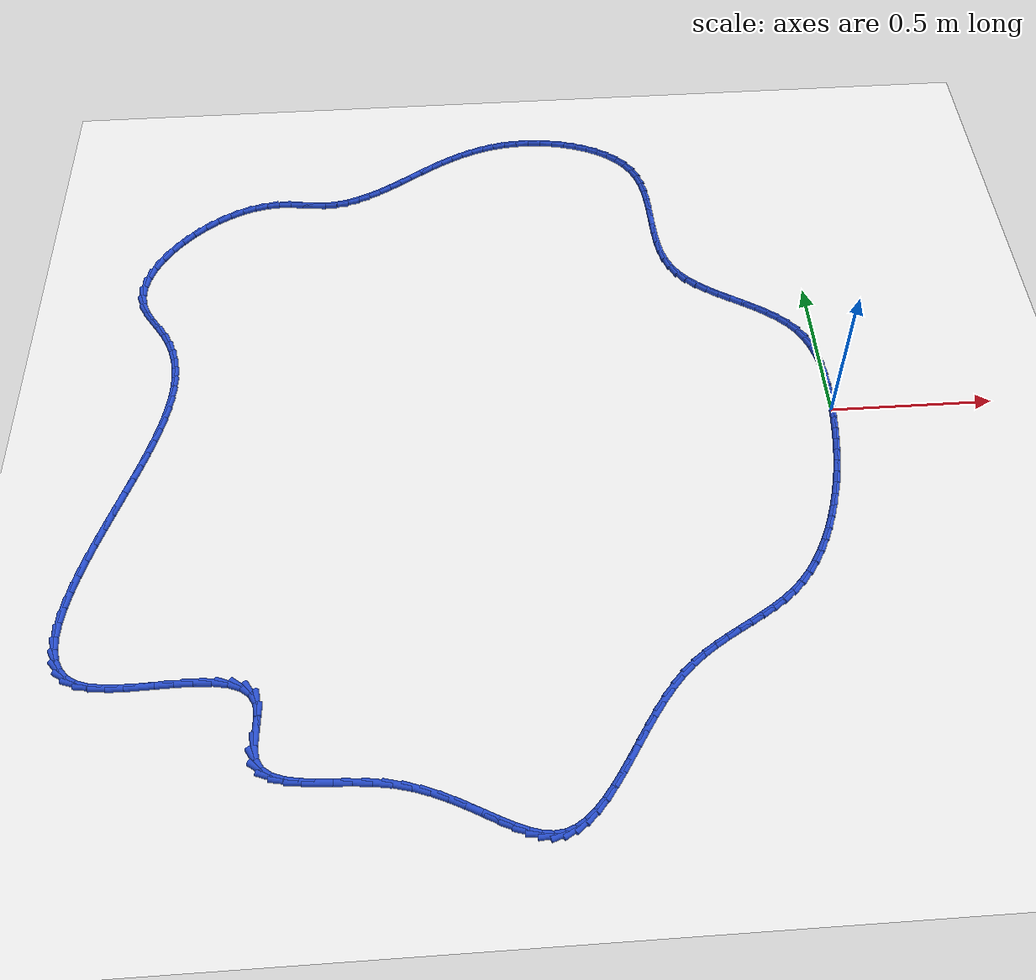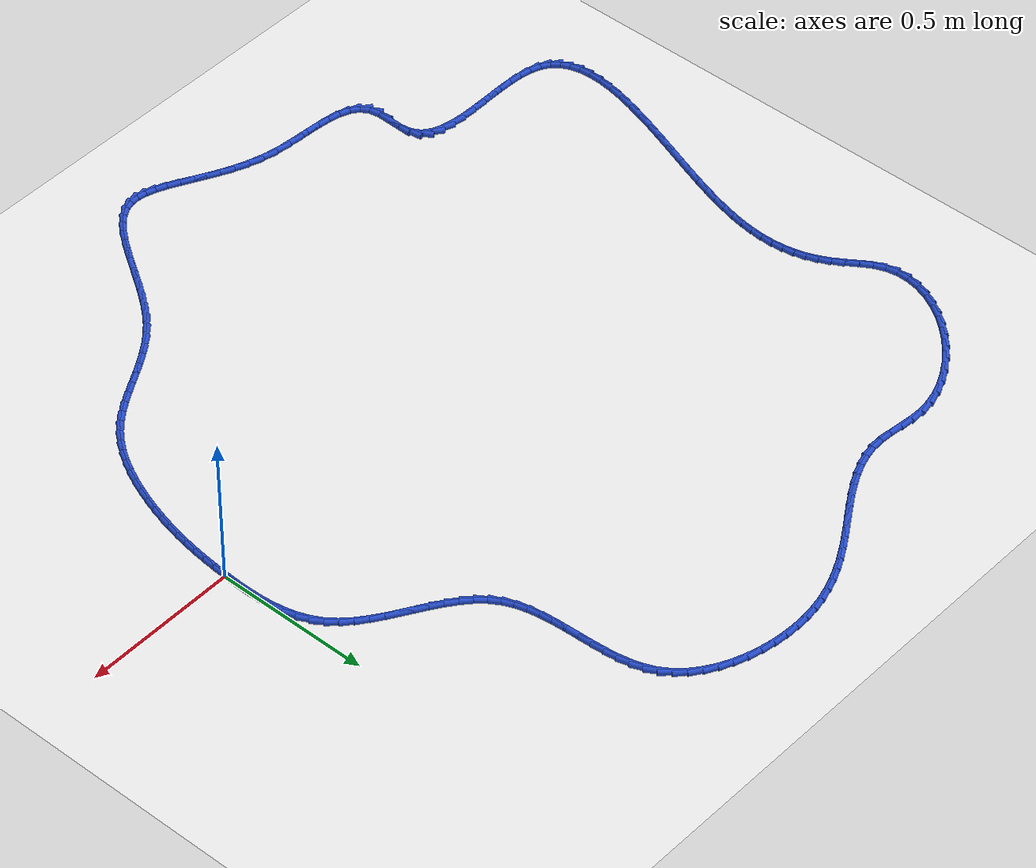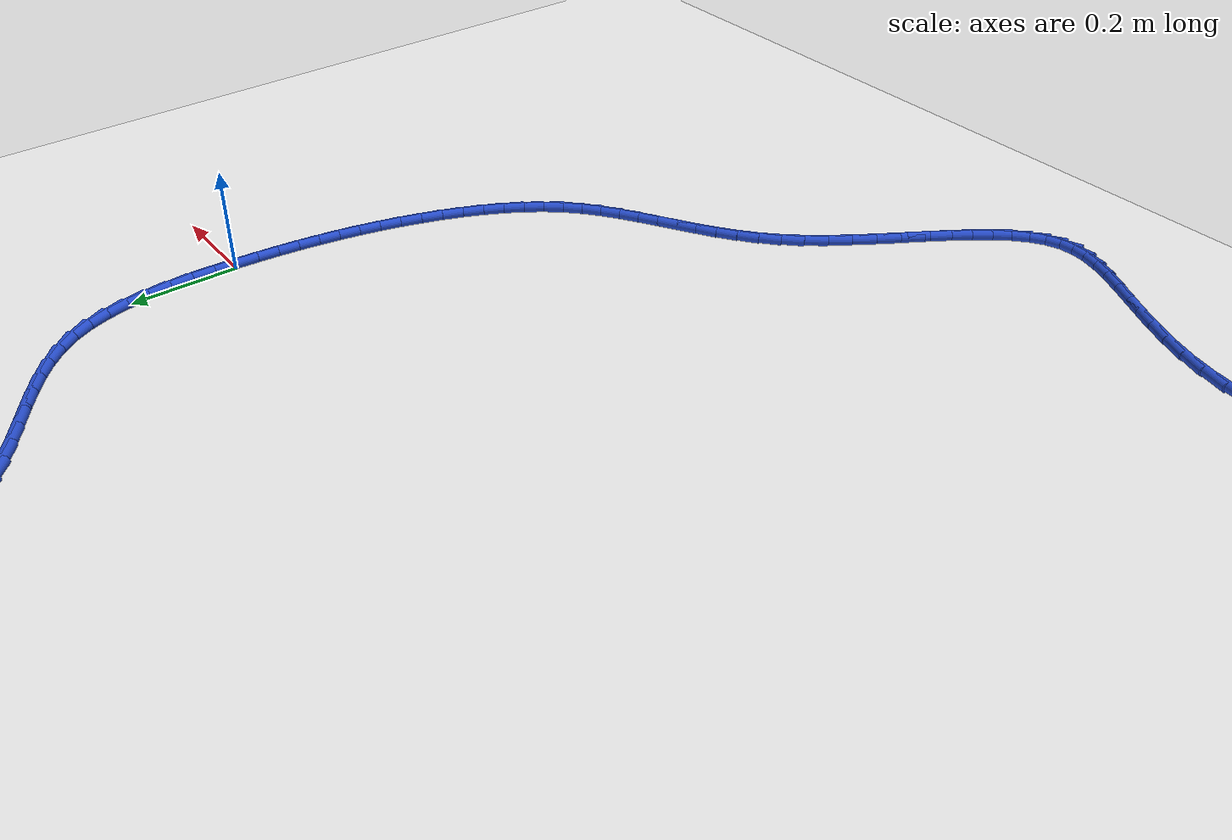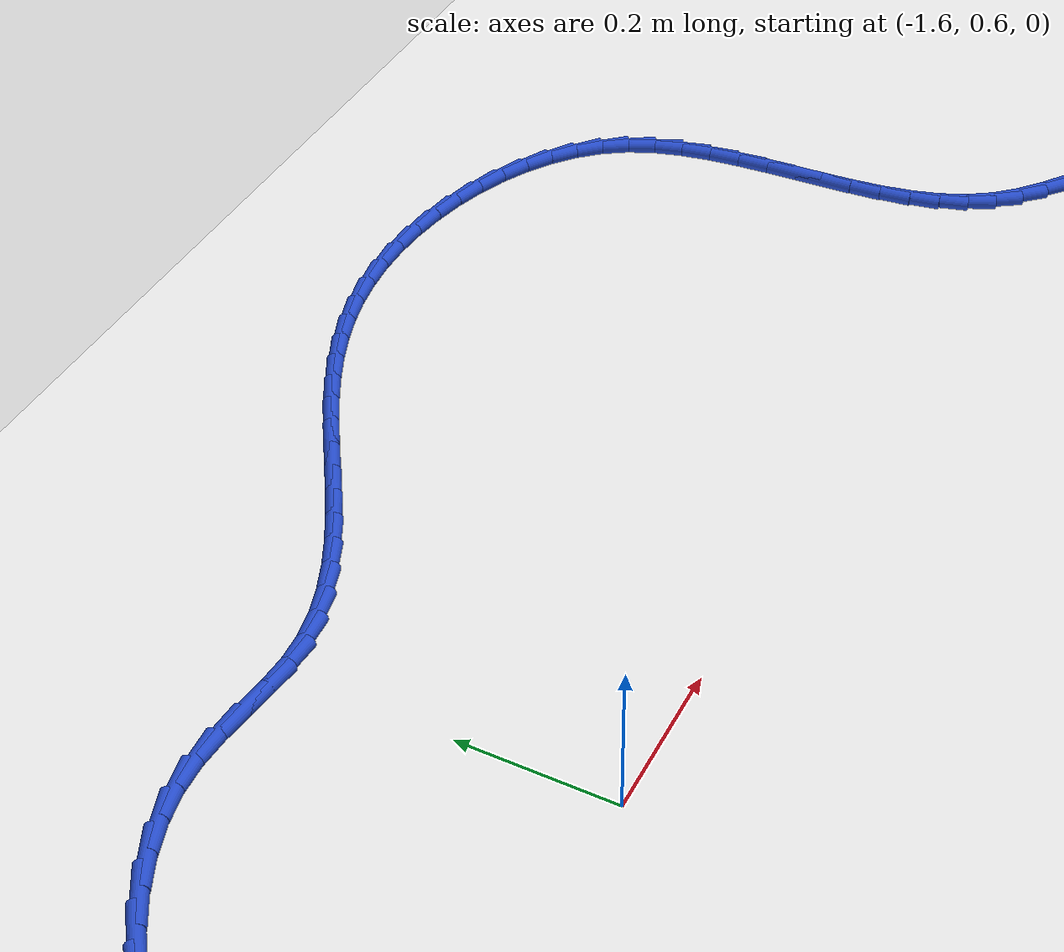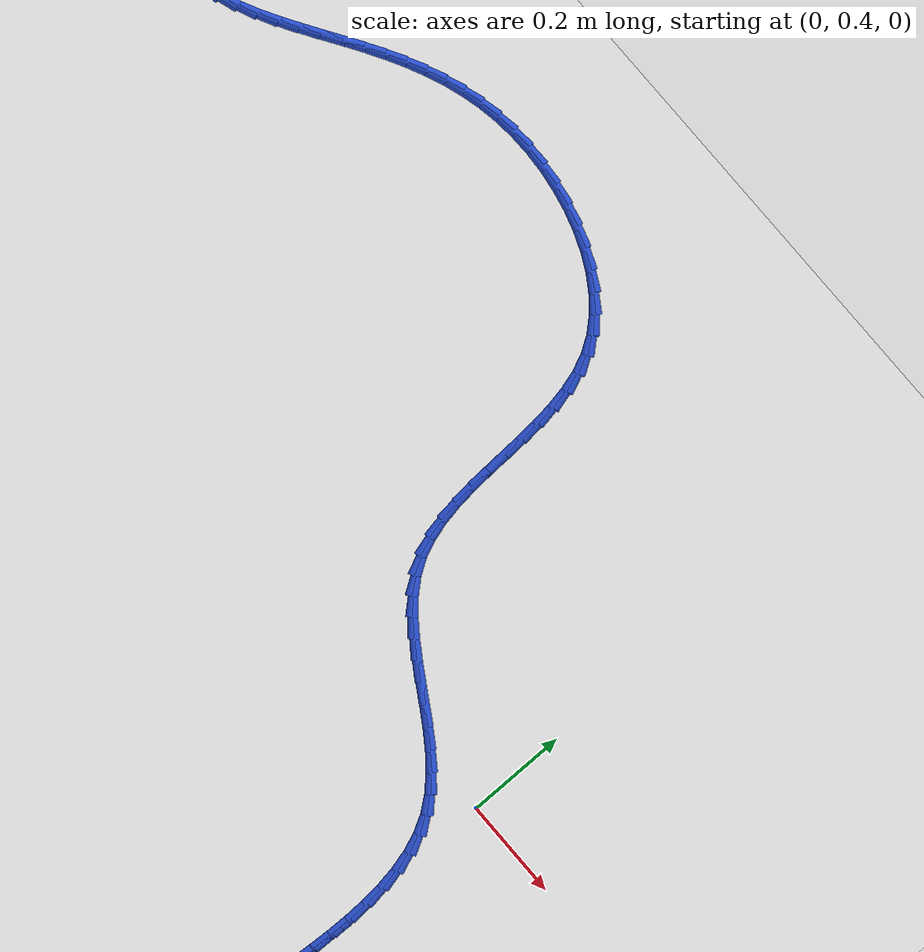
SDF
<sdf version="1.6">
 <world name="default">
  <light name="sun" type="directional">
   <pose>0 0 10 0 -0 0</pose>
   <diffuse>0.8 0.8 0.8 1</diffuse>
   <specular>0.2 0.2 0.2 1</specular>
   <attenuation>
    <range>1000</range>
    <constant>0.9</constant>
    <linear>0.01</linear>
    <quadratic>0.001</quadratic>
   </attenuation>
   <direction>-0.5 0.1 -0.9</direction>
  </light>
  <model name="ground_plane">
   <static>1</static>
   <link name="link">
    <collision name="collision">
     <geometry><plane><normal>0 0 1</normal><size>100 100</size></plane></geometry>
     <surface><friction><ode><mu>100</mu><mu2>50</mu2></ode></friction></surface>
    </collision>
    <visual name="visual">
     <cast_shadows>0</cast_shadows>
     <geometry><plane><normal>0 0 1</normal><size>100 100</size></plane></geometry>
     <material>
      <script><uri>file://media/materials/scripts/gazebo.material</uri><name>Gazebo/WhiteGlow</name></script>
     </material>
    </visual>
   </link>
  </model>
  <gravity>0 0 -9.8</gravity>
  <magnetic_field>6e-06 2.3e-05 -4.2e-05</magnetic_field>
  <atmosphere type="adiabatic"/>
  <physics name="default_physics" default="0" type="ode">
   <max_step_size>0.001</max_step_size>
   <real_time_factor>1</real_time_factor>
   <real_time_update_rate>1000</real_time_update_rate>
  </physics>
  <scene><ambient>0.4 0.4 0.4 1</ambient><background>0.7 0.7 0.7 1</background><shadows>1</shadows></scene>
  <spherical_coordinates>
   <surface_model>EARTH_WGS84</surface_model>
   <latitude_deg>0</latitude_deg>
   <longitude_deg>0</longitude_deg>
   <elevation>0</elevation>
   <heading_deg>0</heading_deg>
  </spherical_coordinates>
  <model name="line">
   <link name="link_0">
    <pose>1.691355389077387e-17 2.0816681711721685e-17 0.01 0 1.57 1.522221613665021</pose>
    <collision name="collision">
     <geometry><cylinder><radius>0.01</radius><length>0.08</length></cylinder></geometry>
    </collision>
    <visual name="visual">
     <material>
      <script><name>Gazebo/Blue</name><uri>file://media/materials/scripts/gazebo.material</uri></script>
     </material>
     <geometry><cylinder><radius>0.01</radius><length>0.08</length></cylinder></geometry>
    </visual>
   </link>
   <link name="link_1">
    <pose>0.0020679108261999067 0.042538267822976816 0.01 0 1.57 1.5533333395738829</pose>
    <collision name="collision">
     <geometry><cylinder><radius>0.01</radius><length>0.08</length></cylinder></geometry>
    </collision>
    <visual name="visual">
     <material>
      <script><name>Gazebo/Blue</name><uri>file://media/materials/scripts/gazebo.material</uri></script>
     </material>
     <geometry><cylinder><radius>0.01</radius><length>0.08</length></cylinder></geometry>
    </visual>
   </link>
   <link name="link_2">
    <pose>0.0028172999088813145 0.08544690050818356 0.01 0 1.57 -1.5443978900608295</pose>
    <collision name="collision">
     <geometry><cylinder><radius>0.01</radius><length>0.08</length></cylinder></geometry>
    </collision>
    <visual name="visual">
     <material>
      <script><name>Gazebo/Blue</name><uri>file://media/materials/scripts/gazebo.material</uri></script>
     </material>
     <geometry><cylinder><radius>0.01</radius><length>0.08</length></cylinder></geometry>
    </visual>
   </link>
   <link name="link_3">
    <pose>0.0016885103330667199 0.12819668018878616 0.01 0 1.57 -1.486203625077718</pose>
    <collision name="collision">
     <geometry><cylinder><radius>0.01</radius><length>0.08</length></cylinder></geometry>
    </collision>
    <visual name="visual">
     <material>
      <script><name>Gazebo/Blue</name><uri>file://media/materials/scripts/gazebo.material</uri></script>
     </material>
     <geometry><cylinder><radius>0.01</radius><length>0.08</length></cylinder></geometry>
    </visual>
   </link>
   <link name="link_4">
    <pose>-0.0018781148162213962 0.1702583889979505 0.01 0 1.57 -1.4114486038348077</pose>
    <collision name="collision">
     <geometry><cylinder><radius>0.01</radius><length>0.08</length></cylinder></geometry>
    </collision>
    <visual name="visual">
     <material>
      <script><name>Gazebo/Blue</name><uri>file://media/materials/scripts/gazebo.material</uri></script>
     </material>
     <geometry><cylinder><radius>0.01</radius><length>0.08</length></cylinder></geometry>
    </visual>
   </link>
   <link name="link_5">
    <pose>-0.00844223245396055 0.21110280906884246 0.01 0 1.57 -1.3174872434004243</pose>
    <collision name="collision">
     <geometry><cylinder><radius>0.01</radius><length>0.08</length></cylinder></geometry>
    </collision>
    <visual name="visual">
     <material>
      <script><name>Gazebo/Blue</name><uri>file://media/materials/scripts/gazebo.material</uri></script>
     </material>
     <geometry><cylinder><radius>0.01</radius><length>0.08</length></cylinder></geometry>
    </visual>
   </link>
   <link name="link_6">
    <pose>-0.01856349949512827 0.2502007225346279 0.01 0 1.57 -1.2018329938862848</pose>
    <collision name="collision">
     <geometry><cylinder><radius>0.01</radius><length>0.08</length></cylinder></geometry>
    </collision>
    <visual name="visual">
     <material>
      <script><name>Gazebo/Blue</name><uri>file://media/materials/scripts/gazebo.material</uri></script>
     </material>
     <geometry><cylinder><radius>0.01</radius><length>0.08</length></cylinder></geometry>
    </visual>
   </link>
   <link name="link_7">
    <pose>-0.03280157285470206 0.28702291152847265 0.01 0 1.57 -1.0633369888944393</pose>
    <collision name="collision">
     <geometry><cylinder><radius>0.01</radius><length>0.08</length></cylinder></geometry>
    </collision>
    <visual name="visual">
     <material>
      <script><name>Gazebo/Blue</name><uri>file://media/materials/scripts/gazebo.material</uri></script>
     </material>
     <geometry><cylinder><radius>0.01</radius><length>0.08</length></cylinder></geometry>
    </visual>
   </link>
   <link name="link_8">
    <pose>-0.05171610944765947 0.3210401581835427 0.01 0 1.57 -0.9095631473061758</pose>
    <collision name="collision">
     <geometry><cylinder><radius>0.01</radius><length>0.08</length></cylinder></geometry>
    </collision>
    <visual name="visual">
     <material>
      <script><name>Gazebo/Blue</name><uri>file://media/materials/scripts/gazebo.material</uri></script>
     </material>
     <geometry><cylinder><radius>0.01</radius><length>0.08</length></cylinder></geometry>
    </visual>
   </link>
   <link name="link_9">
    <pose>-0.07569130028877238 0.35185332037245287 0.01 0 1.57 -0.7767427714807227</pose>
    <collision name="collision">
     <geometry><cylinder><radius>0.01</radius><length>0.08</length></cylinder></geometry>
    </collision>
    <visual name="visual">
     <material>
      <script><name>Gazebo/Blue</name><uri>file://media/materials/scripts/gazebo.material</uri></script>
     </material>
     <geometry><cylinder><radius>0.01</radius><length>0.08</length></cylinder></geometry>
    </visual>
   </link>
   <link name="link_10">
    <pose>-0.104122344304829 0.3797964119656669 0.01 0 1.57 -0.6769317993643341</pose>
    <collision name="collision">
     <geometry><cylinder><radius>0.01</radius><length>0.08</length></cylinder></geometry>
    </collision>
    <visual name="visual">
     <material>
      <script><name>Gazebo/Blue</name><uri>file://media/materials/scripts/gazebo.material</uri></script>
     </material>
     <geometry><cylinder><radius>0.01</radius><length>0.08</length></cylinder></geometry>
    </visual>
   </link>
   <link name="link_11">
    <pose>-0.13605824960355506 0.4054600837455915 0.01 0 1.57 -0.6074608588814171</pose>
    <collision name="collision">
     <geometry><cylinder><radius>0.01</radius><length>0.08</length></cylinder></geometry>
    </collision>
    <visual name="visual">
     <material>
      <script><name>Gazebo/Blue</name><uri>file://media/materials/scripts/gazebo.material</uri></script>
     </material>
     <geometry><cylinder><radius>0.01</radius><length>0.08</length></cylinder></geometry>
    </visual>
   </link>
   <link name="link_12">
    <pose>-0.17054765632889737 0.42943525927219617 0.01 0 1.57 -0.5649573330623945</pose>
    <collision name="collision">
     <geometry><cylinder><radius>0.01</radius><length>0.08</length></cylinder></geometry>
    </collision>
    <visual name="visual">
     <material>
      <script><name>Gazebo/Blue</name><uri>file://media/materials/scripts/gazebo.material</uri></script>
     </material>
     <geometry><cylinder><radius>0.01</radius><length>0.08</length></cylinder></geometry>
    </visual>
   </link>
   <link name="link_13">
    <pose>-0.2066392046248027 0.45231286210545013 0.01 0 1.57 -0.5469091196829627</pose>
    <collision name="collision">
     <geometry><cylinder><radius>0.01</radius><length>0.08</length></cylinder></geometry>
    </collision>
    <visual name="visual">
     <material>
      <script><name>Gazebo/Blue</name><uri>file://media/materials/scripts/gazebo.material</uri></script>
     </material>
     <geometry><cylinder><radius>0.01</radius><length>0.08</length></cylinder></geometry>
    </visual>
   </link>
   <link name="link_14">
    <pose>-0.24338153463521797 0.47468381580532293 0.01 0 1.57 -0.552242615982454</pose>
    <collision name="collision">
     <geometry><cylinder><radius>0.01</radius><length>0.08</length></cylinder></geometry>
    </collision>
    <visual name="visual">
     <material>
      <script><name>Gazebo/Blue</name><uri>file://media/materials/scripts/gazebo.material</uri></script>
     </material>
     <geometry><cylinder><radius>0.01</radius><length>0.08</length></cylinder></geometry>
    </visual>
   </link>
   <link name="link_15">
    <pose>-0.27982328650409005 0.4971390439317838 0.01 0 1.57 -0.5814931289321992</pose>
    <collision name="collision">
     <geometry><cylinder><radius>0.01</radius><length>0.08</length></cylinder></geometry>
    </collision>
    <visual name="visual">
     <material>
      <script><name>Gazebo/Blue</name><uri>file://media/materials/scripts/gazebo.material</uri></script>
     </material>
     <geometry><cylinder><radius>0.01</radius><length>0.08</length></cylinder></geometry>
    </visual>
   </link>
   <link name="link_16">
    <pose>-0.3150131003753659 0.5202694700448024 0.01 0 1.57 -0.6368063362622612</pose>
    <collision name="collision">
     <geometry><cylinder><radius>0.01</radius><length>0.08</length></cylinder></geometry>
    </collision>
    <visual name="visual">
     <material>
      <script><name>Gazebo/Blue</name><uri>file://media/materials/scripts/gazebo.material</uri></script>
     </material>
     <geometry><cylinder><radius>0.01</radius><length>0.08</length></cylinder></geometry>
    </visual>
   </link>
   <link name="link_17">
    <pose>-0.3479996163929922 0.5446660177043481 0.01 0 1.57 -0.7216842728819926</pose>
    <collision name="collision">
     <geometry><cylinder><radius>0.01</radius><length>0.08</length></cylinder></geometry>
    </collision>
    <visual name="visual">
     <material>
      <script><name>Gazebo/Blue</name><uri>file://media/materials/scripts/gazebo.material</uri></script>
     </material>
     <geometry><cylinder><radius>0.01</radius><length>0.08</length></cylinder></geometry>
    </visual>
   </link>
   <link name="link_18">
    <pose>-0.3778314747009158 0.5709196104703902 0.01 0 1.57 -0.8400169934311482</pose>
    <collision name="collision">
     <geometry><cylinder><radius>0.01</radius><length>0.08</length></cylinder></geometry>
    </collision>
    <visual name="visual">
     <material>
      <script><name>Gazebo/Blue</name><uri>file://media/materials/scripts/gazebo.material</uri></script>
     </material>
     <geometry><cylinder><radius>0.01</radius><length>0.08</length></cylinder></geometry>
    </visual>
   </link>
   <link name="link_19">
    <pose>-0.40355731544308376 0.599621171902898 0.01 0 1.57 -0.9932773577039897</pose>
    <collision name="collision">
     <geometry><cylinder><radius>0.01</radius><length>0.08</length></cylinder></geometry>
    </collision>
    <visual name="visual">
     <material>
      <script><name>Gazebo/Blue</name><uri>file://media/materials/scripts/gazebo.material</uri></script>
     </material>
     <geometry><cylinder><radius>0.01</radius><length>0.08</length></cylinder></geometry>
    </visual>
   </link>
   <link name="link_20">
    <pose>-0.42423618079633385 0.6313553196306986 0.01 0 1.57 -1.1564997103995225</pose>
    <collision name="collision">
     <geometry><cylinder><radius>0.01</radius><length>0.08</length></cylinder></geometry>
    </collision>
    <visual name="visual">
     <material>
      <script><name>Gazebo/Blue</name><uri>file://media/materials/scripts/gazebo.material</uri></script>
     </material>
     <geometry><cylinder><radius>0.01</radius><length>0.08</length></cylinder></geometry>
    </visual>
   </link>
   <link name="link_21">
    <pose>-0.4396019917620437 0.6662975455432761 0.01 0 1.57 -1.29006345033564</pose>
    <collision name="collision">
     <geometry><cylinder><radius>0.01</radius><length>0.08</length></cylinder></geometry>
    </collision>
    <visual name="visual">
     <material>
      <script><name>Gazebo/Blue</name><uri>file://media/materials/scripts/gazebo.material</uri></script>
     </material>
     <geometry><cylinder><radius>0.01</radius><length>0.08</length></cylinder></geometry>
    </visual>
   </link>
   <link name="link_22">
    <pose>-0.4504650100484297 0.703970841153073 0.01 0 1.57 -1.3905108438895515</pose>
    <collision name="collision">
     <geometry><cylinder><radius>0.01</radius><length>0.08</length></cylinder></geometry>
    </collision>
    <visual name="visual">
     <material>
      <script><name>Gazebo/Blue</name><uri>file://media/materials/scripts/gazebo.material</uri></script>
     </material>
     <geometry><cylinder><radius>0.01</radius><length>0.08</length></cylinder></geometry>
    </visual>
   </link>
   <link name="link_23">
    <pose>-0.4577317173967378 0.7438398673645454 0.01 0 1.57 -1.4610311942288745</pose>
    <collision name="collision">
     <geometry><cylinder><radius>0.01</radius><length>0.08</length></cylinder></geometry>
    </collision>
    <visual name="visual">
     <material>
      <script><name>Gazebo/Blue</name><uri>file://media/materials/scripts/gazebo.material</uri></script>
     </material>
     <geometry><cylinder><radius>0.01</radius><length>0.08</length></cylinder></geometry>
    </visual>
   </link>
   <link name="link_24">
    <pose>-0.4623085955482127 0.7853692850821493 0.01 0 1.57 -1.5053976260929902</pose>
    <collision name="collision">
     <geometry><cylinder><radius>0.01</radius><length>0.08</length></cylinder></geometry>
    </collision>
    <visual name="visual">
     <material>
      <script><name>Gazebo/Blue</name><uri>file://media/materials/scripts/gazebo.material</uri></script>
     </material>
     <geometry><cylinder><radius>0.01</radius><length>0.08</length></cylinder></geometry>
    </visual>
   </link>
   <link name="link_25">
    <pose>-0.46510212624410013 0.8280237552103414 0.01 0 1.57 -1.5265034010526273</pose>
    <collision name="collision">
     <geometry><cylinder><radius>0.01</radius><length>0.08</length></cylinder></geometry>
    </collision>
    <visual name="visual">
     <material>
      <script><name>Gazebo/Blue</name><uri>file://media/materials/scripts/gazebo.material</uri></script>
     </material>
     <geometry><cylinder><radius>0.01</radius><length>0.08</length></cylinder></geometry>
    </visual>
   </link>
   <link name="link_26">
    <pose>-0.46701879122564516 0.8712679386535777 0.01 0 1.57 -1.5258763141245006</pose>
    <collision name="collision">
     <geometry><cylinder><radius>0.01</radius><length>0.08</length></cylinder></geometry>
    </collision>
    <visual name="visual">
     <material>
      <script><name>Gazebo/Blue</name><uri>file://media/materials/scripts/gazebo.material</uri></script>
     </material>
     <geometry><cylinder><radius>0.01</radius><length>0.08</length></cylinder></geometry>
    </visual>
   </link>
   <link name="link_27">
    <pose>-0.46896507223409306 0.9145664963163141 0.01 0 1.57 -1.5035801102862445</pose>
    <collision name="collision">
     <geometry><cylinder><radius>0.01</radius><length>0.08</length></cylinder></geometry>
    </collision>
    <visual name="visual">
     <material>
      <script><name>Gazebo/Blue</name><uri>file://media/materials/scripts/gazebo.material</uri></script>
     </material>
     <geometry><cylinder><radius>0.01</radius><length>0.08</length></cylinder></geometry>
    </visual>
   </link>
   <link name="link_28">
    <pose>-0.47184745101068926 0.9573840891030071 0.01 0 1.57 -1.4582402726657926</pose>
    <collision name="collision">
     <geometry><cylinder><radius>0.01</radius><length>0.08</length></cylinder></geometry>
    </collision>
    <visual name="visual">
     <material>
      <script><name>Gazebo/Blue</name><uri>file://media/materials/scripts/gazebo.material</uri></script>
     </material>
     <geometry><cylinder><radius>0.01</radius><length>0.08</length></cylinder></geometry>
    </visual>
   </link>
   <link name="link_29">
    <pose>-0.476572409296679 0.9991853779181132 0.01 0 1.57 -1.3871959680780457</pose>
    <collision name="collision">
     <geometry><cylinder><radius>0.01</radius><length>0.08</length></cylinder></geometry>
    </collision>
    <visual name="visual">
     <material>
      <script><name>Gazebo/Blue</name><uri>file://media/materials/scripts/gazebo.material</uri></script>
     </material>
     <geometry><cylinder><radius>0.01</radius><length>0.08</length></cylinder></geometry>
    </visual>
   </link>
   <link name="link_30">
    <pose>-0.48404642883330745 1.039435023666088 0.01 0 1.57 -1.2870315435014392</pose>
    <collision name="collision">
     <geometry><cylinder><radius>0.01</radius><length>0.08</length></cylinder></geometry>
    </collision>
    <visual name="visual">
     <material>
      <script><name>Gazebo/Blue</name><uri>file://media/materials/scripts/gazebo.material</uri></script>
     </material>
     <geometry><cylinder><radius>0.01</radius><length>0.08</length></cylinder></geometry>
    </visual>
   </link>
   <link name="link_31">
    <pose>-0.49517599136182033 1.0775976872513888 0.01 0 1.57 -1.155021056296306</pose>
    <collision name="collision">
     <geometry><cylinder><radius>0.01</radius><length>0.08</length></cylinder></geometry>
    </collision>
    <visual name="visual">
     <material>
      <script><name>Gazebo/Blue</name><uri>file://media/materials/scripts/gazebo.material</uri></script>
     </material>
     <geometry><cylinder><radius>0.01</radius><length>0.08</length></cylinder></geometry>
    </visual>
   </link>
   <link name="link_32">
    <pose>-0.5108675786234624 1.1131380295784703 0.01 0 1.57 -0.9947271172294986</pose>
    <collision name="collision">
     <geometry><cylinder><radius>0.01</radius><length>0.08</length></cylinder></geometry>
    </collision>
    <visual name="visual">
     <material>
      <script><name>Gazebo/Blue</name><uri>file://media/materials/scripts/gazebo.material</uri></script>
     </material>
     <geometry><cylinder><radius>0.01</radius><length>0.08</length></cylinder></geometry>
    </visual>
   </link>
   <link name="link_33">
    <pose>-0.5319247623001148 1.145555402155814 0.01 0 1.57 -0.8366649857890878</pose>
    <collision name="collision">
     <geometry><cylinder><radius>0.01</radius><length>0.08</length></cylinder></geometry>
    </collision>
    <visual name="visual">
     <material>
      <script><name>Gazebo/Blue</name><uri>file://media/materials/scripts/gazebo.material</uri></script>
     </material>
     <geometry><cylinder><radius>0.01</radius><length>0.08</length></cylinder></geometry>
    </visual>
   </link>
   <link name="link_34">
    <pose>-0.5581978076402031 1.174670512598399 0.01 0 1.57 -0.6970692271816917</pose>
    <collision name="collision">
     <geometry><cylinder><radius>0.01</radius><length>0.08</length></cylinder></geometry>
    </collision>
    <visual name="visual">
     <material>
      <script><name>Gazebo/Blue</name><uri>file://media/materials/scripts/gazebo.material</uri></script>
     </material>
     <geometry><cylinder><radius>0.01</radius><length>0.08</length></cylinder></geometry>
    </visual>
   </link>
   <link name="link_35">
    <pose>-0.5890205901844026 1.2004781416000117 0.01 0 1.57 -0.5751749426472138</pose>
    <collision name="collision">
     <geometry><cylinder><radius>0.01</radius><length>0.08</length></cylinder></geometry>
    </collision>
    <visual name="visual">
     <material>
      <script><name>Gazebo/Blue</name><uri>file://media/materials/scripts/gazebo.material</uri></script>
     </material>
     <geometry><cylinder><radius>0.01</radius><length>0.08</length></cylinder></geometry>
    </visual>
   </link>
   <link name="link_36">
    <pose>-0.623721893773296 1.2229747862478875 0.01 0 1.57 -0.46844451210125737</pose>
    <collision name="collision">
     <geometry><cylinder><radius>0.01</radius><length>0.08</length></cylinder></geometry>
    </collision>
    <visual name="visual">
     <material>
      <script><name>Gazebo/Blue</name><uri>file://media/materials/scripts/gazebo.material</uri></script>
     </material>
     <geometry><cylinder><radius>0.01</radius><length>0.08</length></cylinder></geometry>
    </visual>
   </link>
   <link name="link_37">
    <pose>-0.6616305022474658 1.2421569436292614 0.01 0 1.57 -0.37380185613797756</pose>
    <collision name="collision">
     <geometry><cylinder><radius>0.01</radius><length>0.08</length></cylinder></geometry>
    </collision>
    <visual name="visual">
     <material>
      <script><name>Gazebo/Blue</name><uri>file://media/materials/scripts/gazebo.material</uri></script>
     </material>
     <geometry><cylinder><radius>0.01</radius><length>0.08</length></cylinder></geometry>
    </visual>
   </link>
   <link name="link_38">
    <pose>-0.7020751994474957 1.2580211108313704 0.01 0 1.57 -0.2881967867711691</pose>
    <collision name="collision">
     <geometry><cylinder><radius>0.01</radius><length>0.08</length></cylinder></geometry>
    </collision>
    <visual name="visual">
     <material>
      <script><name>Gazebo/Blue</name><uri>file://media/materials/scripts/gazebo.material</uri></script>
     </material>
     <geometry><cylinder><radius>0.01</radius><length>0.08</length></cylinder></geometry>
    </visual>
   </link>
   <link name="link_39">
    <pose>-0.7443847692139681 1.2705637849414477 0.01 0 1.57 -0.2087968252785894</pose>
    <collision name="collision">
     <geometry><cylinder><radius>0.01</radius><length>0.08</length></cylinder></geometry>
    </collision>
    <visual name="visual">
     <material>
      <script><name>Gazebo/Blue</name><uri>file://media/materials/scripts/gazebo.material</uri></script>
     </material>
     <geometry><cylinder><radius>0.01</radius><length>0.08</length></cylinder></geometry>
    </visual>
   </link>
   <link name="link_40">
    <pose>-0.7878879953874665 1.2797814630467303 0.01 0 1.57 -0.13297755218350366</pose>
    <collision name="collision">
     <geometry><cylinder><radius>0.01</radius><length>0.08</length></cylinder></geometry>
    </collision>
    <visual name="visual">
     <material>
      <script><name>Gazebo/Blue</name><uri>file://media/materials/scripts/gazebo.material</uri></script>
     </material>
     <geometry><cylinder><radius>0.01</radius><length>0.08</length></cylinder></geometry>
    </visual>
   </link>
   <link name="link_41">
    <pose>-0.831913661808573 1.2856706422344526 0.01 0 1.57 -0.05821488123679092</pose>
    <collision name="collision">
     <geometry><cylinder><radius>0.01</radius><length>0.08</length></cylinder></geometry>
    </collision>
    <visual name="visual">
     <material>
      <script><name>Gazebo/Blue</name><uri>file://media/materials/scripts/gazebo.material</uri></script>
     </material>
     <geometry><cylinder><radius>0.01</radius><length>0.08</length></cylinder></geometry>
    </visual>
   </link>
   <link name="link_42">
    <pose>-0.8757905523178712 1.288227819591851 0.01 0 1.57 0.01807474883514695</pose>
    <collision name="collision">
     <geometry><cylinder><radius>0.01</radius><length>0.08</length></cylinder></geometry>
    </collision>
    <visual name="visual">
     <material>
      <script><name>Gazebo/Blue</name><uri>file://media/materials/scripts/gazebo.material</uri></script>
     </material>
     <geometry><cylinder><radius>0.01</radius><length>0.08</length></cylinder></geometry>
    </visual>
   </link>
   <link name="link_43">
    <pose>-0.9188474507559437 1.2874494922061603 0.01 0 1.57 0.09762130438071634</pose>
    <collision name="collision">
     <geometry><cylinder><radius>0.01</radius><length>0.08</length></cylinder></geometry>
    </collision>
    <visual name="visual">
     <material>
      <script><name>Gazebo/Blue</name><uri>file://media/materials/scripts/gazebo.material</uri></script>
     </material>
     <geometry><cylinder><radius>0.01</radius><length>0.08</length></cylinder></geometry>
    </visual>
   </link>
   <link name="link_44">
    <pose>-0.9605462645519919 1.283365819004701 0.01 0 1.57 0.17685050622496032</pose>
    <collision name="collision">
     <geometry><cylinder><radius>0.01</radius><length>0.08</length></cylinder></geometry>
    </collision>
    <visual name="visual">
     <material>
      <script><name>Gazebo/Blue</name><uri>file://media/materials/scripts/gazebo.material</uri></script>
     </material>
     <geometry><cylinder><radius>0.01</radius><length>0.08</length></cylinder></geometry>
    </visual>
   </link>
   <link name="link_45">
    <pose>-1.0009175764749982 1.2761507550560138 0.01 0 1.57 0.25282234450929825</pose>
    <collision name="collision">
     <geometry><cylinder><radius>0.01</radius><length>0.08</length></cylinder></geometry>
    </collision>
    <visual name="visual">
     <material>
      <script><name>Gazebo/Blue</name><uri>file://media/materials/scripts/gazebo.material</uri></script>
     </material>
     <geometry><cylinder><radius>0.01</radius><length>0.08</length></cylinder></geometry>
    </visual>
   </link>
   <link name="link_46">
    <pose>-1.0401437896134809 1.2660166449535204 0.01 0 1.57 0.32377916667781625</pose>
    <collision name="collision">
     <geometry><cylinder><radius>0.01</radius><length>0.08</length></cylinder></geometry>
    </collision>
    <visual name="visual">
     <material>
      <script><name>Gazebo/Blue</name><uri>file://media/materials/scripts/gazebo.material</uri></script>
     </material>
     <geometry><cylinder><radius>0.01</radius><length>0.08</length></cylinder></geometry>
    </visual>
   </link>
   <link name="link_47">
    <pose>-1.0784073085515882 1.2531758336688323 0.01 0 1.57 0.38834429451031227</pose>
    <collision name="collision">
     <geometry><cylinder><radius>0.01</radius><length>0.08</length></cylinder></geometry>
    </collision>
    <visual name="visual">
     <material>
      <script><name>Gazebo/Blue</name><uri>file://media/materials/scripts/gazebo.material</uri></script>
     </material>
     <geometry><cylinder><radius>0.01</radius><length>0.08</length></cylinder></geometry>
    </visual>
   </link>
   <link name="link_48">
    <pose>-1.1158905378734696 1.237840666173561 0.01 0 1.57 0.44558386274883416</pose>
    <collision name="collision">
     <geometry><cylinder><radius>0.01</radius><length>0.08</length></cylinder></geometry>
    </collision>
    <visual name="visual">
     <material>
      <script><name>Gazebo/Blue</name><uri>file://media/materials/scripts/gazebo.material</uri></script>
     </material>
     <geometry><cylinder><radius>0.01</radius><length>0.08</length></cylinder></geometry>
    </visual>
   </link>
   <link name="link_49">
    <pose>-1.1527758821632736 1.2202234874393172 0.01 0 1.57 0.49498716236648876</pose>
    <collision name="collision">
     <geometry><cylinder><radius>0.01</radius><length>0.08</length></cylinder></geometry>
    </collision>
    <visual name="visual">
     <material>
      <script><name>Gazebo/Blue</name><uri>file://media/materials/scripts/gazebo.material</uri></script>
     </material>
     <geometry><cylinder><radius>0.01</radius><length>0.08</length></cylinder></geometry>
    </visual>
   </link>
   <link name="link_50">
    <pose>-1.1892457460051495 1.200536642437711 0.01 0 1.57 0.5350274507627867</pose>
    <collision name="collision">
     <geometry><cylinder><radius>0.01</radius><length>0.08</length></cylinder></geometry>
    </collision>
    <visual name="visual">
     <material>
      <script><name>Gazebo/Blue</name><uri>file://media/materials/scripts/gazebo.material</uri></script>
     </material>
     <geometry><cylinder><radius>0.01</radius><length>0.08</length></cylinder></geometry>
    </visual>
   </link>
   <link name="link_51">
    <pose>-1.225466038004763 1.179069223443069 0.01 0 1.57 0.5606889858278536</pose>
    <collision name="collision">
     <geometry><cylinder><radius>0.01</radius><length>0.08</length></cylinder></geometry>
    </collision>
    <visual name="visual">
     <material>
      <script><name>Gazebo/Blue</name><uri>file://media/materials/scripts/gazebo.material</uri></script>
     </material>
     <geometry><cylinder><radius>0.01</radius><length>0.08</length></cylinder></geometry>
    </visual>
   </link>
   <link name="link_52">
    <pose>-1.2615359866756075 1.1564205508998384 0.01 0 1.57 0.5714965667115651</pose>
    <collision name="collision">
     <geometry><cylinder><radius>0.01</radius><length>0.08</length></cylinder></geometry>
    </collision>
    <visual name="visual">
     <material>
      <script><name>Gazebo/Blue</name><uri>file://media/materials/scripts/gazebo.material</uri></script>
     </material>
     <geometry><cylinder><radius>0.01</radius><length>0.08</length></cylinder></geometry>
    </visual>
   </link>
   <link name="link_53">
    <pose>-1.2975379746312117 1.1332683205598484 0.01 0 1.57 0.5678856188450359</pose>
    <collision name="collision">
     <geometry><cylinder><radius>0.01</radius><length>0.08</length></cylinder></geometry>
    </collision>
    <visual name="visual">
     <material>
      <script><name>Gazebo/Blue</name><uri>file://media/materials/scripts/gazebo.material</uri></script>
     </material>
     <geometry><cylinder><radius>0.01</radius><length>0.08</length></cylinder></geometry>
    </visual>
   </link>
   <link name="link_54">
    <pose>-1.3335543844843898 1.1102902281782472 0.01 0 1.57 0.5496992422400554</pose>
    <collision name="collision">
     <geometry><cylinder><radius>0.01</radius><length>0.08</length></cylinder></geometry>
    </collision>
    <visual name="visual">
     <material>
      <script><name>Gazebo/Blue</name><uri>file://media/materials/scripts/gazebo.material</uri></script>
     </material>
     <geometry><cylinder><radius>0.01</radius><length>0.08</length></cylinder></geometry>
    </visual>
   </link>
   <link name="link_55">
    <pose>-1.3696675988479563 1.0881639695101841 0.01 0 1.57 0.5161960572456934</pose>
    <collision name="collision">
     <geometry><cylinder><radius>0.01</radius><length>0.08</length></cylinder></geometry>
    </collision>
    <visual name="visual">
     <material>
      <script><name>Gazebo/Blue</name><uri>file://media/materials/scripts/gazebo.material</uri></script>
     </material>
     <geometry><cylinder><radius>0.01</radius><length>0.08</length></cylinder></geometry>
    </visual>
   </link>
   <link name="link_56">
    <pose>-1.4059600003347255 1.067567240310809 0.01 0 1.57 0.46610709047637916</pose>
    <collision name="collision">
     <geometry><cylinder><radius>0.01</radius><length>0.08</length></cylinder></geometry>
    </collision>
    <visual name="visual">
     <material>
      <script><name>Gazebo/Blue</name><uri>file://media/materials/scripts/gazebo.material</uri></script>
     </material>
     <geometry><cylinder><radius>0.01</radius><length>0.08</length></cylinder></geometry>
    </visual>
   </link>
   <link name="link_57">
    <pose>-1.4425139715575126 1.0491777363352714 0.01 0 1.57 0.3977997289657891</pose>
    <collision name="collision">
     <geometry><cylinder><radius>0.01</radius><length>0.08</length></cylinder></geometry>
    </collision>
    <visual name="visual">
     <material>
      <script><name>Gazebo/Blue</name><uri>file://media/materials/scripts/gazebo.material</uri></script>
     </material>
     <geometry><cylinder><radius>0.01</radius><length>0.08</length></cylinder></geometry>
    </visual>
   </link>
   <link name="link_58">
    <pose>-1.479411895129131 1.0336731533387193 0.01 0 1.57 0.3096592833879768</pose>
    <collision name="collision">
     <geometry><cylinder><radius>0.01</radius><length>0.08</length></cylinder></geometry>
    </collision>
    <visual name="visual">
     <material>
      <script><name>Gazebo/Blue</name><uri>file://media/materials/scripts/gazebo.material</uri></script>
     </material>
     <geometry><cylinder><radius>0.01</radius><length>0.08</length></cylinder></geometry>
    </visual>
   </link>
   <link name="link_59">
    <pose>-1.5167361536623967 1.021731187076304 0.01 0 1.57 0.2008257523492841</pose>
    <collision name="collision">
     <geometry><cylinder><radius>0.01</radius><length>0.08</length></cylinder></geometry>
    </collision>
    <visual name="visual">
     <material>
      <script><name>Gazebo/Blue</name><uri>file://media/materials/scripts/gazebo.material</uri></script>
     </material>
     <geometry><cylinder><radius>0.01</radius><length>0.08</length></cylinder></geometry>
    </visual>
   </link>
   <link name="link_60">
    <pose>-1.5545691297701227 1.0140295333031728 0.01 0 1.57 0.07232447256842135</pose>
    <collision name="collision">
     <geometry><cylinder><radius>0.01</radius><length>0.08</length></cylinder></geometry>
    </collision>
    <visual name="visual">
     <material>
      <script><name>Gazebo/Blue</name><uri>file://media/materials/scripts/gazebo.material</uri></script>
     </material>
     <geometry><cylinder><radius>0.01</radius><length>0.08</length></cylinder></geometry>
    </visual>
   </link>
   <link name="link_61">
    <pose>-1.5929932055738625 1.011245676633504 0.01 0 1.57 -0.054188244656737626</pose>
    <collision name="collision">
     <geometry><cylinder><radius>0.01</radius><length>0.08</length></cylinder></geometry>
    </collision>
    <visual name="visual">
     <material>
      <script><name>Gazebo/Blue</name><uri>file://media/materials/scripts/gazebo.material</uri></script>
     </material>
     <geometry><cylinder><radius>0.01</radius><length>0.08</length></cylinder></geometry>
    </visual>
   </link>
   <link name="link_62">
    <pose>-1.6320891558927666 1.013366293596658 0.01 0 1.57 -0.11950139520040619</pose>
    <collision name="collision">
     <geometry><cylinder><radius>0.01</radius><length>0.08</length></cylinder></geometry>
    </collision>
    <visual name="visual">
     <material>
      <script><name>Gazebo/Blue</name><uri>file://media/materials/scripts/gazebo.material</uri></script>
     </material>
     <geometry><cylinder><radius>0.01</radius><length>0.08</length></cylinder></geometry>
    </visual>
   </link>
   <link name="link_63">
    <pose>-1.6719325725261487 1.0181504326168003 0.01 0 1.57 -0.11648715165361215</pose>
    <collision name="collision">
     <geometry><cylinder><radius>0.01</radius><length>0.08</length></cylinder></geometry>
    </collision>
    <visual name="visual">
     <material>
      <script><name>Gazebo/Blue</name><uri>file://media/materials/scripts/gazebo.material</uri></script>
     </material>
     <geometry><cylinder><radius>0.01</radius><length>0.08</length></cylinder></geometry>
    </visual>
   </link>
   <link name="link_64">
    <pose>-1.7125980045251417 1.0229089757541316 0.01 0 1.57 -0.049135854828193784</pose>
    <collision name="collision">
     <geometry><cylinder><radius>0.01</radius><length>0.08</length></cylinder></geometry>
    </collision>
    <visual name="visual">
     <material>
      <script><name>Gazebo/Blue</name><uri>file://media/materials/scripts/gazebo.material</uri></script>
     </material>
     <geometry><cylinder><radius>0.01</radius><length>0.08</length></cylinder></geometry>
    </visual>
   </link>
   <link name="link_65">
    <pose>-1.7541600009408793 1.0249528050688523 0.01 0 1.57 0.07701813627680969</pose>
    <collision name="collision">
     <geometry><cylinder><radius>0.01</radius><length>0.08</length></cylinder></geometry>
    </collision>
    <visual name="visual">
     <material>
      <script><name>Gazebo/Blue</name><uri>file://media/materials/scripts/gazebo.material</uri></script>
     </material>
     <geometry><cylinder><radius>0.01</radius><length>0.08</length></cylinder></geometry>
    </visual>
   </link>
   <link name="link_66">
    <pose>-1.7966757400261755 1.0216718321641316 0.01 0 1.57 0.21865178752225276</pose>
    <collision name="collision">
     <geometry><cylinder><radius>0.01</radius><length>0.08</length></cylinder></geometry>
    </collision>
    <visual name="visual">
     <material>
      <script><name>Gazebo/Blue</name><uri>file://media/materials/scripts/gazebo.material</uri></script>
     </material>
     <geometry><cylinder><radius>0.01</radius><length>0.08</length></cylinder></geometry>
    </visual>
   </link>
   <link name="link_67">
    <pose>-1.8398455874431876 1.012079310037524 0.01 0 1.57 0.34186766257549467</pose>
    <collision name="collision">
     <geometry><cylinder><radius>0.01</radius><length>0.08</length></cylinder></geometry>
    </collision>
    <visual name="visual">
     <material>
      <script><name>Gazebo/Blue</name><uri>file://media/materials/scripts/gazebo.material</uri></script>
     </material>
     <geometry><cylinder><radius>0.01</radius><length>0.08</length></cylinder></geometry>
    </visual>
   </link>
   <link name="link_68">
    <pose>-1.88303532794312 0.9967106886514344 0.01 0 1.57 0.4498183488337492</pose>
    <collision name="collision">
     <geometry><cylinder><radius>0.01</radius><length>0.08</length></cylinder></geometry>
    </collision>
    <visual name="visual">
     <material>
      <script><name>Gazebo/Blue</name><uri>file://media/materials/scripts/gazebo.material</uri></script>
     </material>
     <geometry><cylinder><radius>0.01</radius><length>0.08</length></cylinder></geometry>
    </visual>
   </link>
   <link name="link_69">
    <pose>-1.9255978275841434 0.9761601923773388 0.01 0 1.57 0.5468991917893983</pose>
    <collision name="collision">
     <geometry><cylinder><radius>0.01</radius><length>0.08</length></cylinder></geometry>
    </collision>
    <visual name="visual">
     <material>
      <script><name>Gazebo/Blue</name><uri>file://media/materials/scripts/gazebo.material</uri></script>
     </material>
     <geometry><cylinder><radius>0.01</radius><length>0.08</length></cylinder></geometry>
    </visual>
   </link>
   <link name="link_70">
    <pose>-1.9668859524244278 0.951022045586713 0.01 0 1.57 0.6370748763090639</pose>
    <collision name="collision">
     <geometry><cylinder><radius>0.01</radius><length>0.08</length></cylinder></geometry>
    </collision>
    <visual name="visual">
     <material>
      <script><name>Gazebo/Blue</name><uri>file://media/materials/scripts/gazebo.material</uri></script>
     </material>
     <geometry><cylinder><radius>0.01</radius><length>0.08</length></cylinder></geometry>
    </visual>
   </link>
   <link name="link_71">
    <pose>-2.0062525685221435 0.9218904726510323 0.01 0 1.57 0.7239255077234509</pose>
    <collision name="collision">
     <geometry><cylinder><radius>0.01</radius><length>0.08</length></cylinder></geometry>
    </collision>
    <visual name="visual">
     <material>
      <script><name>Gazebo/Blue</name><uri>file://media/materials/scripts/gazebo.material</uri></script>
     </material>
     <geometry><cylinder><radius>0.01</radius><length>0.08</length></cylinder></geometry>
    </visual>
   </link>
   <link name="link_72">
    <pose>-2.0430505419354614 0.8893596979417729 0.01 0 1.57 0.8108367767140033</pose>
    <collision name="collision">
     <geometry><cylinder><radius>0.01</radius><length>0.08</length></cylinder></geometry>
    </collision>
    <visual name="visual">
     <material>
      <script><name>Gazebo/Blue</name><uri>file://media/materials/scripts/gazebo.material</uri></script>
     </material>
     <geometry><cylinder><radius>0.01</radius><length>0.08</length></cylinder></geometry>
    </visual>
   </link>
   <link name="link_73">
    <pose>-2.076632738722551 0.8540239458304107 0.01 0 1.57 0.9012397456134732</pose>
    <collision name="collision">
     <geometry><cylinder><radius>0.01</radius><length>0.08</length></cylinder></geometry>
    </collision>
    <visual name="visual">
     <material>
      <script><name>Gazebo/Blue</name><uri>file://media/materials/scripts/gazebo.material</uri></script>
     </material>
     <geometry><cylinder><radius>0.01</radius><length>0.08</length></cylinder></geometry>
    </visual>
   </link>
   <link name="link_74">
    <pose>-2.106352024941583 0.8164774406884208 0.01 0 1.57 0.9988627425494536</pose>
    <collision name="collision">
     <geometry><cylinder><radius>0.01</radius><length>0.08</length></cylinder></geometry>
    </collision>
    <visual name="visual">
     <material>
      <script><name>Gazebo/Blue</name><uri>file://media/materials/scripts/gazebo.material</uri></script>
     </material>
     <geometry><cylinder><radius>0.01</radius><length>0.08</length></cylinder></geometry>
    </visual>
   </link>
   <link name="link_75">
    <pose>-2.1315612666507273 0.7773144068872793 0.01 0 1.57 1.107957414676053</pose>
    <collision name="collision">
     <geometry><cylinder><radius>0.01</radius><length>0.08</length></cylinder></geometry>
    </collision>
    <visual name="visual">
     <material>
      <script><name>Gazebo/Blue</name><uri>file://media/materials/scripts/gazebo.material</uri></script>
     </material>
     <geometry><cylinder><radius>0.01</radius><length>0.08</length></cylinder></geometry>
    </visual>
   </link>
   <link name="link_76">
    <pose>-2.1516133299081543 0.7371290687984621 0.01 0 1.57 1.233396628866156</pose>
    <collision name="collision">
     <geometry><cylinder><radius>0.01</radius><length>0.08</length></cylinder></geometry>
    </collision>
    <visual name="visual">
     <material>
      <script><name>Gazebo/Blue</name><uri>file://media/materials/scripts/gazebo.material</uri></script>
     </material>
     <geometry><cylinder><radius>0.01</radius><length>0.08</length></cylinder></geometry>
    </visual>
   </link>
   <link name="link_77">
    <pose>-2.1658610807720353 0.6965156507934444 0.01 0 1.57 1.3803793341223702</pose>
    <collision name="collision">
     <geometry><cylinder><radius>0.01</radius><length>0.08</length></cylinder></geometry>
    </collision>
    <visual name="visual">
     <material>
      <script><name>Gazebo/Blue</name><uri>file://media/materials/scripts/gazebo.material</uri></script>
     </material>
     <geometry><cylinder><radius>0.01</radius><length>0.08</length></cylinder></geometry>
    </visual>
   </link>
   <link name="link_78">
    <pose>-2.1736573853005394 0.6560683772437024 0.01 0 1.57 1.5532174204802034</pose>
    <collision name="collision">
     <geometry><cylinder><radius>0.01</radius><length>0.08</length></cylinder></geometry>
    </collision>
    <visual name="visual">
     <material>
      <script><name>Gazebo/Blue</name><uri>file://media/materials/scripts/gazebo.material</uri></script>
     </material>
     <geometry><cylinder><radius>0.01</radius><length>0.08</length></cylinder></geometry>
    </visual>
   </link>
   <link name="link_79">
    <pose>-2.1743551095518376 0.6163814725207115 0.01 0 1.57 -1.3889617307788928</pose>
    <collision name="collision">
     <geometry><cylinder><radius>0.01</radius><length>0.08</length></cylinder></geometry>
    </collision>
    <visual name="visual">
     <material>
      <script><name>Gazebo/Blue</name><uri>file://media/materials/scripts/gazebo.material</uri></script>
     </material>
     <geometry><cylinder><radius>0.01</radius><length>0.08</length></cylinder></geometry>
    </visual>
   </link>
   <link name="link_80">
    <pose>-2.1673071195840996 0.578049160995948 0.01 0 1.57 -1.1770648980191345</pose>
    <collision name="collision">
     <geometry><cylinder><radius>0.01</radius><length>0.08</length></cylinder></geometry>
    </collision>
    <visual name="visual">
     <material>
      <script><name>Gazebo/Blue</name><uri>file://media/materials/scripts/gazebo.material</uri></script>
     </material>
     <geometry><cylinder><radius>0.01</radius><length>0.08</length></cylinder></geometry>
    </visual>
   </link>
   <link name="link_81">
    <pose>-2.152155101548543 0.5415754992739868 0.01 0 1.57 -1.028555798903717</pose>
    <collision name="collision">
     <geometry><cylinder><radius>0.01</radius><length>0.08</length></cylinder></geometry>
    </collision>
    <visual name="visual">
     <material>
      <script><name>Gazebo/Blue</name><uri>file://media/materials/scripts/gazebo.material</uri></script>
     </material>
     <geometry><cylinder><radius>0.01</radius><length>0.08</length></cylinder></geometry>
    </visual>
   </link>
   <link name="link_82">
    <pose>-2.1311190098894524 0.506659625257229 0.01 0 1.57 -0.9702361472218114</pose>
    <collision name="collision">
     <geometry><cylinder><radius>0.01</radius><length>0.08</length></cylinder></geometry>
    </collision>
    <visual name="visual">
     <material>
      <script><name>Gazebo/Blue</name><uri>file://media/materials/scripts/gazebo.material</uri></script>
     </material>
     <geometry><cylinder><radius>0.01</radius><length>0.08</length></cylinder></geometry>
    </visual>
   </link>
   <link name="link_83">
    <pose>-2.107774162813605 0.47257754103881555 0.01 0 1.57 -0.9947265599944293</pose>
    <collision name="collision">
     <geometry><cylinder><radius>0.01</radius><length>0.08</length></cylinder></geometry>
    </collision>
    <visual name="visual">
     <material>
      <script><name>Gazebo/Blue</name><uri>file://media/materials/scripts/gazebo.material</uri></script>
     </material>
     <geometry><cylinder><radius>0.01</radius><length>0.08</length></cylinder></geometry>
    </visual>
   </link>
   <link name="link_84">
    <pose>-2.085704841245808 0.4386020313940095 0.01 0 1.57 -1.0840519718375454</pose>
    <collision name="collision">
     <geometry><cylinder><radius>0.01</radius><length>0.08</length></cylinder></geometry>
    </collision>
    <visual name="visual">
     <material>
      <script><name>Gazebo/Blue</name><uri>file://media/materials/scripts/gazebo.material</uri></script>
     </material>
     <geometry><cylinder><radius>0.01</radius><length>0.08</length></cylinder></geometry>
    </visual>
   </link>
   <link name="link_85">
    <pose>-2.06749014250951 0.4041835993552184 0.01 0 1.57 -1.1845356110066656</pose>
    <collision name="collision">
     <geometry><cylinder><radius>0.01</radius><length>0.08</length></cylinder></geometry>
    </collision>
    <visual name="visual">
     <material>
      <script><name>Gazebo/Blue</name><uri>file://media/materials/scripts/gazebo.material</uri></script>
     </material>
     <geometry><cylinder><radius>0.01</radius><length>0.08</length></cylinder></geometry>
    </visual>
   </link>
   <link name="link_86">
    <pose>-2.053264654469166 0.3692049415959308 0.01 0 1.57 -1.284796349332241</pose>
    <collision name="collision">
     <geometry><cylinder><radius>0.01</radius><length>0.08</length></cylinder></geometry>
    </collision>
    <visual name="visual">
     <material>
      <script><name>Gazebo/Blue</name><uri>file://media/materials/scripts/gazebo.material</uri></script>
     </material>
     <geometry><cylinder><radius>0.01</radius><length>0.08</length></cylinder></geometry>
    </visual>
   </link>
   <link name="link_87">
    <pose>-2.042798484028493 0.33361319567487824 0.01 0 1.57 -1.3817627180207424</pose>
    <collision name="collision">
     <geometry><cylinder><radius>0.01</radius><length>0.08</length></cylinder></geometry>
    </collision>
    <visual name="visual">
     <material>
      <script><name>Gazebo/Blue</name><uri>file://media/materials/scripts/gazebo.material</uri></script>
     </material>
     <geometry><cylinder><radius>0.01</radius><length>0.08</length></cylinder></geometry>
    </visual>
   </link>
   <link name="link_88">
    <pose>-2.0358617380912114 0.2973554991507932 0.01 0 1.57 -1.4727462067079893</pose>
    <collision name="collision">
     <geometry><cylinder><radius>0.01</radius><length>0.08</length></cylinder></geometry>
    </collision>
    <visual name="visual">
     <material>
      <script><name>Gazebo/Blue</name><uri>file://media/materials/scripts/gazebo.material</uri></script>
     </material>
     <geometry><cylinder><radius>0.01</radius><length>0.08</length></cylinder></geometry>
    </visual>
   </link>
   <link name="link_89">
    <pose>-2.0322245235610374 0.2603789895824081 0.01 0 1.57 -1.5557616051950147</pose>
    <collision name="collision">
     <geometry><cylinder><radius>0.01</radius><length>0.08</length></cylinder></geometry>
    </collision>
    <visual name="visual">
     <material>
      <script><name>Gazebo/Blue</name><uri>file://media/materials/scripts/gazebo.material</uri></script>
     </material>
     <geometry><cylinder><radius>0.01</radius><length>0.08</length></cylinder></geometry>
    </visual>
   </link>
   <link name="link_90">
    <pose>-2.03165694734169 0.2226308045284557 0.01 0 1.57 1.5119582103994458</pose>
    <collision name="collision">
     <geometry><cylinder><radius>0.01</radius><length>0.08</length></cylinder></geometry>
    </collision>
    <visual name="visual">
     <material>
      <script><name>Gazebo/Blue</name><uri>file://media/materials/scripts/gazebo.material</uri></script>
     </material>
     <geometry><cylinder><radius>0.01</radius><length>0.08</length></cylinder></geometry>
    </visual>
   </link>
   <link name="link_91">
    <pose>-2.033929116336887 0.1840580815476673 0.01 0 1.57 1.4476705838248731</pose>
    <collision name="collision">
     <geometry><cylinder><radius>0.01</radius><length>0.08</length></cylinder></geometry>
    </collision>
    <visual name="visual">
     <material>
      <script><name>Gazebo/Blue</name><uri>file://media/materials/scripts/gazebo.material</uri></script>
     </material>
     <geometry><cylinder><radius>0.01</radius><length>0.08</length></cylinder></geometry>
    </visual>
   </link>
   <link name="link_92">
    <pose>-2.0388111374503466 0.14460795819877573 0.01 0 1.57 1.3928590555230238</pose>
    <collision name="collision">
     <geometry><cylinder><radius>0.01</radius><length>0.08</length></cylinder></geometry>
    </collision>
    <visual name="visual">
     <material>
      <script><name>Gazebo/Blue</name><uri>file://media/materials/scripts/gazebo.material</uri></script>
     </material>
     <geometry><cylinder><radius>0.01</radius><length>0.08</length></cylinder></geometry>
    </visual>
   </link>
   <link name="link_93">
    <pose>-2.046073117585786 0.10422757204051356 0.01 0 1.57 1.3470611661634657</pose>
    <collision name="collision">
     <geometry><cylinder><radius>0.01</radius><length>0.08</length></cylinder></geometry>
    </collision>
    <visual name="visual">
     <material>
      <script><name>Gazebo/Blue</name><uri>file://media/materials/scripts/gazebo.material</uri></script>
     </material>
     <geometry><cylinder><radius>0.01</radius><length>0.08</length></cylinder></geometry>
    </visual>
   </link>
   <link name="link_94">
    <pose>-2.0554851636469245 0.06286406063161228 0.01 0 1.57 1.3096284355116887</pose>
    <collision name="collision">
     <geometry><cylinder><radius>0.01</radius><length>0.08</length></cylinder></geometry>
    </collision>
    <visual name="visual">
     <material>
      <script><name>Gazebo/Blue</name><uri>file://media/materials/scripts/gazebo.material</uri></script>
     </material>
     <geometry><cylinder><radius>0.01</radius><length>0.08</length></cylinder></geometry>
    </visual>
   </link>
   <link name="link_95">
    <pose>-2.06681738253748 0.020464561530804573 0.01 0 1.57 1.2798460434341905</pose>
    <collision name="collision">
     <geometry><cylinder><radius>0.01</radius><length>0.08</length></cylinder></geometry>
    </collision>
    <visual name="visual">
     <material>
      <script><name>Gazebo/Blue</name><uri>file://media/materials/scripts/gazebo.material</uri></script>
     </material>
     <geometry><cylinder><radius>0.01</radius><length>0.08</length></cylinder></geometry>
    </visual>
   </link>
   <link name="link_96">
    <pose>-2.0798398811611696 -0.023023787703177215 0.01 0 1.57 1.2570080060791842</pose>
    <collision name="collision">
     <geometry><cylinder><radius>0.01</radius><length>0.08</length></cylinder></geometry>
    </collision>
    <visual name="visual">
     <material>
      <script><name>Gazebo/Blue</name><uri>file://media/materials/scripts/gazebo.material</uri></script>
     </material>
     <geometry><cylinder><radius>0.01</radius><length>0.08</length></cylinder></geometry>
    </visual>
   </link>
   <link name="link_97">
    <pose>-2.094322766421713 -0.06765384951160092 0.01 0 1.57 1.2404584591201449</pose>
    <collision name="collision">
     <geometry><cylinder><radius>0.01</radius><length>0.08</length></cylinder></geometry>
    </collision>
    <visual name="visual">
     <material>
      <script><name>Gazebo/Blue</name><uri>file://media/materials/scripts/gazebo.material</uri></script>
     </material>
     <geometry><cylinder><radius>0.01</radius><length>0.08</length></cylinder></geometry>
    </visual>
   </link>
   <link name="link_98">
    <pose>-2.1100361452228267 -0.11347848633573318 0.01 0 1.57 1.2296101175125167</pose>
    <collision name="collision">
     <geometry><cylinder><radius>0.01</radius><length>0.08</length></cylinder></geometry>
    </collision>
    <visual name="visual">
     <material>
      <script><name>Gazebo/Blue</name><uri>file://media/materials/scripts/gazebo.material</uri></script>
     </material>
     <geometry><cylinder><radius>0.01</radius><length>0.08</length></cylinder></geometry>
    </visual>
   </link>
   <link name="link_99">
    <pose>-2.126750124468229 -0.16055056061684367 0.01 0 1.57 1.2239487047864324</pose>
    <collision name="collision">
     <geometry><cylinder><radius>0.01</radius><length>0.08</length></cylinder></geometry>
    </collision>
    <visual name="visual">
     <material>
      <script><name>Gazebo/Blue</name><uri>file://media/materials/scripts/gazebo.material</uri></script>
     </material>
     <geometry><cylinder><radius>0.01</radius><length>0.08</length></cylinder></geometry>
    </visual>
   </link>
   <link name="link_100">
    <pose>-2.144234811061639 -0.20892293479619922 0.01 0 1.57 1.2233792428943173</pose>
    <collision name="collision">
     <geometry><cylinder><radius>0.01</radius><length>0.08</length></cylinder></geometry>
    </collision>
    <visual name="visual">
     <material>
      <script><name>Gazebo/Blue</name><uri>file://media/materials/scripts/gazebo.material</uri></script>
     </material>
     <geometry><cylinder><radius>0.01</radius><length>0.08</length></cylinder></geometry>
    </visual>
   </link>
   <link name="link_101">
    <pose>-2.1622088958355783 -0.2585608192185805 0.01 0 1.57 1.2291232249358977</pose>
    <collision name="collision">
     <geometry><cylinder><radius>0.01</radius><length>0.08</length></cylinder></geometry>
    </collision>
    <visual name="visual">
     <material>
      <script><name>Gazebo/Blue</name><uri>file://media/materials/scripts/gazebo.material</uri></script>
     </material>
     <geometry><cylinder><radius>0.01</radius><length>0.08</length></cylinder></geometry>
    </visual>
   </link>
   <link name="link_102">
    <pose>-2.1801567661497687 -0.3090299928811828 0.01 0 1.57 1.2415841698358405</pose>
    <collision name="collision">
     <geometry><cylinder><radius>0.01</radius><length>0.08</length></cylinder></geometry>
    </collision>
    <visual name="visual">
     <material>
      <script><name>Gazebo/Blue</name><uri>file://media/materials/scripts/gazebo.material</uri></script>
     </material>
     <geometry><cylinder><radius>0.01</radius><length>0.08</length></cylinder></geometry>
    </visual>
   </link>
   <link name="link_103">
    <pose>-2.197496103934227 -0.35978251798751165 0.01 0 1.57 1.2612309321381425</pose>
    <collision name="collision">
     <geometry><cylinder><radius>0.01</radius><length>0.08</length></cylinder></geometry>
    </collision>
    <visual name="visual">
     <material>
      <script><name>Gazebo/Blue</name><uri>file://media/materials/scripts/gazebo.material</uri></script>
     </material>
     <geometry><cylinder><radius>0.01</radius><length>0.08</length></cylinder></geometry>
    </visual>
   </link>
   <link name="link_104">
    <pose>-2.2136445863140106 -0.41027044854976086 0.01 0 1.57 1.2891064494950186</pose>
    <collision name="collision">
     <geometry><cylinder><radius>0.01</radius><length>0.08</length></cylinder></geometry>
    </collision>
    <visual name="visual">
     <material>
      <script><name>Gazebo/Blue</name><uri>file://media/materials/scripts/gazebo.material</uri></script>
     </material>
     <geometry><cylinder><radius>0.01</radius><length>0.08</length></cylinder></geometry>
    </visual>
   </link>
   <link name="link_105">
    <pose>-2.2280198904141733 -0.45994583858012367 0.01 0 1.57 1.3269658139705232</pose>
    <collision name="collision">
     <geometry><cylinder><radius>0.01</radius><length>0.08</length></cylinder></geometry>
    </collision>
    <visual name="visual">
     <material>
      <script><name>Gazebo/Blue</name><uri>file://media/materials/scripts/gazebo.material</uri></script>
     </material>
     <geometry><cylinder><radius>0.01</radius><length>0.08</length></cylinder></geometry>
    </visual>
   </link>
   <link name="link_106">
    <pose>-2.240039693359772 -0.5082607420907963 0.01 0 1.57 1.377533954431387</pose>
    <collision name="collision">
     <geometry><cylinder><radius>0.01</radius><length>0.08</length></cylinder></geometry>
    </collision>
    <visual name="visual">
     <material>
      <script><name>Gazebo/Blue</name><uri>file://media/materials/scripts/gazebo.material</uri></script>
     </material>
     <geometry><cylinder><radius>0.01</radius><length>0.08</length></cylinder></geometry>
    </visual>
   </link>
   <link name="link_107">
    <pose>-2.249121672275864 -0.554667213093972 0.01 0 1.57 1.4449166395568367</pose>
    <collision name="collision">
     <geometry><cylinder><radius>0.01</radius><length>0.08</length></cylinder></geometry>
    </collision>
    <visual name="visual">
     <material>
      <script><name>Gazebo/Blue</name><uri>file://media/materials/scripts/gazebo.material</uri></script>
     </material>
     <geometry><cylinder><radius>0.01</radius><length>0.08</length></cylinder></geometry>
    </visual>
   </link>
   <link name="link_108">
    <pose>-2.2546835042875015 -0.5986173056018445 0.01 0 1.57 1.5351700623992117</pose>
    <collision name="collision">
     <geometry><cylinder><radius>0.01</radius><length>0.08</length></cylinder></geometry>
    </collision>
    <visual name="visual">
     <material>
      <script><name>Gazebo/Blue</name><uri>file://media/materials/scripts/gazebo.material</uri></script>
     </material>
     <geometry><cylinder><radius>0.01</radius><length>0.08</length></cylinder></geometry>
    </visual>
   </link>
   <link name="link_109">
    <pose>-2.2561428665197423 -0.639563073626608 0.01 0 1.57 -1.4847528460484904</pose>
    <collision name="collision">
     <geometry><cylinder><radius>0.01</radius><length>0.08</length></cylinder></geometry>
    </collision>
    <visual name="visual">
     <material>
      <script><name>Gazebo/Blue</name><uri>file://media/materials/scripts/gazebo.material</uri></script>
     </material>
     <geometry><cylinder><radius>0.01</radius><length>0.08</length></cylinder></geometry>
    </visual>
   </link>
   <link name="link_110">
    <pose>-2.2529174360976416 -0.6769565711804569 0.01 0 1.57 -1.3210395296468112</pose>
    <collision name="collision">
     <geometry><cylinder><radius>0.01</radius><length>0.08</length></cylinder></geometry>
    </collision>
    <visual name="visual">
     <material>
      <script><name>Gazebo/Blue</name><uri>file://media/materials/scripts/gazebo.material</uri></script>
     </material>
     <geometry><cylinder><radius>0.01</radius><length>0.08</length></cylinder></geometry>
    </visual>
   </link>
   <link name="link_111">
    <pose>-2.2444248901462553 -0.7102498522755851 0.01 0 1.57 -1.1066063632792311</pose>
    <collision name="collision">
     <geometry><cylinder><radius>0.01</radius><length>0.08</length></cylinder></geometry>
    </collision>
    <visual name="visual">
     <material>
      <script><name>Gazebo/Blue</name><uri>file://media/materials/scripts/gazebo.material</uri></script>
     </material>
     <geometry><cylinder><radius>0.01</radius><length>0.08</length></cylinder></geometry>
    </visual>
   </link>
   <link name="link_112">
    <pose>-2.230082905790639 -0.7388949709241861 0.01 0 1.57 -0.8458197302458234</pose>
    <collision name="collision">
     <geometry><cylinder><radius>0.01</radius><length>0.08</length></cylinder></geometry>
    </collision>
    <visual name="visual">
     <material>
      <script><name>Gazebo/Blue</name><uri>file://media/materials/scripts/gazebo.material</uri></script>
     </material>
     <geometry><cylinder><radius>0.01</radius><length>0.08</length></cylinder></geometry>
    </visual>
   </link>
   <link name="link_113">
    <pose>-2.2093091601558488 -0.7623439811384555 0.01 0 1.57 -0.5672871893802495</pose>
    <collision name="collision">
     <geometry><cylinder><radius>0.01</radius><length>0.08</length></cylinder></geometry>
    </collision>
    <visual name="visual">
     <material>
      <script><name>Gazebo/Blue</name><uri>file://media/materials/scripts/gazebo.material</uri></script>
     </material>
     <geometry><cylinder><radius>0.01</radius><length>0.08</length></cylinder></geometry>
    </visual>
   </link>
   <link name="link_114">
    <pose>-2.18152133036694 -0.7800489369305863 0.01 0 1.57 -0.31913042103423206</pose>
    <collision name="collision">
     <geometry><cylinder><radius>0.01</radius><length>0.08</length></cylinder></geometry>
    </collision>
    <visual name="visual">
     <material>
      <script><name>Gazebo/Blue</name><uri>file://media/materials/scripts/gazebo.material</uri></script>
     </material>
     <geometry><cylinder><radius>0.01</radius><length>0.08</length></cylinder></geometry>
    </visual>
   </link>
   <link name="link_115">
    <pose>-2.146370628346538 -0.7916635938596357 0.01 0 1.57 -0.1533088516838959</pose>
    <collision name="collision">
     <geometry><cylinder><radius>0.01</radius><length>0.08</length></cylinder></geometry>
    </collision>
    <visual name="visual">
     <material>
      <script><name>Gazebo/Blue</name><uri>file://media/materials/scripts/gazebo.material</uri></script>
     </material>
     <geometry><cylinder><radius>0.01</radius><length>0.08</length></cylinder></geometry>
    </visual>
   </link>
   <link name="link_116">
    <pose>-2.1049274580633615 -0.7980674487188175 0.01 0 1.57 -0.05485361118301497</pose>
    <collision name="collision">
     <geometry><cylinder><radius>0.01</radius><length>0.08</length></cylinder></geometry>
    </collision>
    <visual name="visual">
     <material>
      <script><name>Gazebo/Blue</name><uri>file://media/materials/scripts/gazebo.material</uri></script>
     </material>
     <geometry><cylinder><radius>0.01</radius><length>0.08</length></cylinder></geometry>
    </visual>
   </link>
   <link name="link_117">
    <pose>-2.0587954027663504 -0.8006004996343147 0.01 0 1.57 -6.238779145859056e-05</pose>
    <collision name="collision">
     <geometry><cylinder><radius>0.01</radius><length>0.08</length></cylinder></geometry>
    </collision>
    <visual name="visual">
     <material>
      <script><name>Gazebo/Blue</name><uri>file://media/materials/scripts/gazebo.material</uri></script>
     </material>
     <geometry><cylinder><radius>0.01</radius><length>0.08</length></cylinder></geometry>
    </visual>
   </link>
   <link name="link_118">
    <pose>-2.0095790013773076 -0.8006035701369049 0.01 0 1.57 0.02339169090901133</pose>
    <collision name="collision">
     <geometry><cylinder><radius>0.01</radius><length>0.08</length></cylinder></geometry>
    </collision>
    <visual name="visual">
     <material>
      <script><name>Gazebo/Blue</name><uri>file://media/materials/scripts/gazebo.material</uri></script>
     </material>
     <geometry><cylinder><radius>0.01</radius><length>0.08</length></cylinder></geometry>
    </visual>
   </link>
   <link name="link_119">
    <pose>-1.9588827928180343 -0.7994174837573652 0.01 0 1.57 0.020451755978274155</pose>
    <collision name="collision">
     <geometry><cylinder><radius>0.01</radius><length>0.08</length></cylinder></geometry>
    </collision>
    <visual name="visual">
     <material>
      <script><name>Gazebo/Blue</name><uri>file://media/materials/scripts/gazebo.material</uri></script>
     </material>
     <geometry><cylinder><radius>0.01</radius><length>0.08</length></cylinder></geometry>
    </visual>
   </link>
   <link name="link_120">
    <pose>-1.9083113160103355 -0.798383064026474 0.01 0 1.57 -0.009378303218004664</pose>
    <collision name="collision">
     <geometry><cylinder><radius>0.01</radius><length>0.08</length></cylinder></geometry>
    </collision>
    <visual name="visual">
     <material>
      <script><name>Gazebo/Blue</name><uri>file://media/materials/scripts/gazebo.material</uri></script>
     </material>
     <geometry><cylinder><radius>0.01</radius><length>0.08</length></cylinder></geometry>
    </visual>
   </link>
   <link name="link_121">
    <pose>-1.8594691098760128 -0.7988411344750079 0.01 0 1.57 -0.07219905373736173</pose>
    <collision name="collision">
     <geometry><cylinder><radius>0.01</radius><length>0.08</length></cylinder></geometry>
    </collision>
    <visual name="visual">
     <material>
      <script><name>Gazebo/Blue</name><uri>file://media/materials/scripts/gazebo.material</uri></script>
     </material>
     <geometry><cylinder><radius>0.01</radius><length>0.08</length></cylinder></geometry>
    </visual>
   </link>
   <link name="link_122">
    <pose>-1.8139607133368698 -0.8021325186337454 0.01 0 1.57 -0.18197976721288006</pose>
    <collision name="collision">
     <geometry><cylinder><radius>0.01</radius><length>0.08</length></cylinder></geometry>
    </collision>
    <visual name="visual">
     <material>
      <script><name>Gazebo/Blue</name><uri>file://media/materials/scripts/gazebo.material</uri></script>
     </material>
     <geometry><cylinder><radius>0.01</radius><length>0.08</length></cylinder></geometry>
    </visual>
   </link>
   <link name="link_123">
    <pose>-1.7733906653147091 -0.8095980400334633 0.01 0 1.57 -0.36443452154591427</pose>
    <collision name="collision">
     <geometry><cylinder><radius>0.01</radius><length>0.08</length></cylinder></geometry>
    </collision>
    <visual name="visual">
     <material>
      <script><name>Gazebo/Blue</name><uri>file://media/materials/scripts/gazebo.material</uri></script>
     </material>
     <geometry><cylinder><radius>0.01</radius><length>0.08</length></cylinder></geometry>
    </visual>
   </link>
   <link name="link_124">
    <pose>-1.7393635047313338 -0.8225785222049393 0.01 0 1.57 -0.653964365005562</pose>
    <collision name="collision">
     <geometry><cylinder><radius>0.01</radius><length>0.08</length></cylinder></geometry>
    </collision>
    <visual name="visual">
     <material>
      <script><name>Gazebo/Blue</name><uri>file://media/materials/scripts/gazebo.material</uri></script>
     </material>
     <geometry><cylinder><radius>0.01</radius><length>0.08</length></cylinder></geometry>
    </visual>
   </link>
   <link name="link_125">
    <pose>-1.7134837705085482 -0.8424147886789508 0.01 0 1.57 -1.0487243872912162</pose>
    <collision name="collision">
     <geometry><cylinder><radius>0.01</radius><length>0.08</length></cylinder></geometry>
    </collision>
    <visual name="visual">
     <material>
      <script><name>Gazebo/Blue</name><uri>file://media/materials/scripts/gazebo.material</uri></script>
     </material>
     <geometry><cylinder><radius>0.01</radius><length>0.08</length></cylinder></geometry>
    </visual>
   </link>
   <link name="link_126">
    <pose>-1.6973560015681528 -0.8704476629862762 0.01 0 1.57 -1.427787630046161</pose>
    <collision name="collision">
     <geometry><cylinder><radius>0.01</radius><length>0.08</length></cylinder></geometry>
    </collision>
    <visual name="visual">
     <material>
      <script><name>Gazebo/Blue</name><uri>file://media/materials/scripts/gazebo.material</uri></script>
     </material>
     <geometry><cylinder><radius>0.01</radius><length>0.08</length></cylinder></geometry>
    </visual>
   </link>
   <link name="link_127">
    <pose>-1.6920162541055233 -0.9075313923599044 0.01 0 1.57 1.5390617087024814</pose>
    <collision name="collision">
     <geometry><cylinder><radius>0.01</radius><length>0.08</length></cylinder></geometry>
    </collision>
    <visual name="visual">
     <material>
      <script><name>Gazebo/Blue</name><uri>file://media/materials/scripts/gazebo.material</uri></script>
     </material>
     <geometry><cylinder><radius>0.01</radius><length>0.08</length></cylinder></geometry>
    </visual>
   </link>
   <link name="link_128">
    <pose>-1.6933684808335114 -0.9501275489412196 0.01 0 1.57 1.5417915136584794</pose>
    <collision name="collision">
     <geometry><cylinder><radius>0.01</radius><length>0.08</length></cylinder></geometry>
    </collision>
    <visual name="visual">
     <material>
      <script><name>Gazebo/Blue</name><uri>file://media/materials/scripts/gazebo.material</uri></script>
     </material>
     <geometry><cylinder><radius>0.01</radius><length>0.08</length></cylinder></geometry>
    </visual>
   </link>
   <link name="link_129">
    <pose>-1.6945939814431132 -0.992367329002741 0.01 0 1.57 -1.4141296116409428</pose>
    <collision name="collision">
     <geometry><cylinder><radius>0.01</radius><length>0.08</length></cylinder></geometry>
    </collision>
    <visual name="visual">
     <material>
      <script><name>Gazebo/Blue</name><uri>file://media/materials/scripts/gazebo.material</uri></script>
     </material>
     <geometry><cylinder><radius>0.01</radius><length>0.08</length></cylinder></geometry>
    </visual>
   </link>
   <link name="link_130">
    <pose>-1.6889010569929148 -1.0284073485316039 0.01 0 1.57 -1.024013712310412</pose>
    <collision name="collision">
     <geometry><cylinder><radius>0.01</radius><length>0.08</length></cylinder></geometry>
    </collision>
    <visual name="visual">
     <material>
      <script><name>Gazebo/Blue</name><uri>file://media/materials/scripts/gazebo.material</uri></script>
     </material>
     <geometry><cylinder><radius>0.01</radius><length>0.08</length></cylinder></geometry>
    </visual>
   </link>
   <link name="link_131">
    <pose>-1.6725964805879485 -1.0551938138599144 0.01 0 1.57 -0.6291468821400598</pose>
    <collision name="collision">
     <geometry><cylinder><radius>0.01</radius><length>0.08</length></cylinder></geometry>
    </collision>
    <visual name="visual">
     <material>
      <script><name>Gazebo/Blue</name><uri>file://media/materials/scripts/gazebo.material</uri></script>
     </material>
     <geometry><cylinder><radius>0.01</radius><length>0.08</length></cylinder></geometry>
    </visual>
   </link>
   <link name="link_132">
    <pose>-1.646777037152199 -1.0739854345543252 0.01 0 1.57 -0.352015694917814</pose>
    <collision name="collision">
     <geometry><cylinder><radius>0.01</radius><length>0.08</length></cylinder></geometry>
    </collision>
    <visual name="visual">
     <material>
      <script><name>Gazebo/Blue</name><uri>file://media/materials/scripts/gazebo.material</uri></script>
     </material>
     <geometry><cylinder><radius>0.01</radius><length>0.08</length></cylinder></geometry>
    </visual>
   </link>
   <link name="link_133">
    <pose>-1.6129500841875053 -1.086410563438529 0.01 0 1.57 -0.18835637947128026</pose>
    <collision name="collision">
     <geometry><cylinder><radius>0.01</radius><length>0.08</length></cylinder></geometry>
    </collision>
    <visual name="visual">
     <material>
      <script><name>Gazebo/Blue</name><uri>file://media/materials/scripts/gazebo.material</uri></script>
     </material>
     <geometry><cylinder><radius>0.01</radius><length>0.08</length></cylinder></geometry>
    </visual>
   </link>
   <link name="link_134">
    <pose>-1.5726229791957076 -1.0940975533362183 0.01 0 1.57 -0.10065633530572332</pose>
    <collision name="collision">
     <geometry><cylinder><radius>0.01</radius><length>0.08</length></cylinder></geometry>
    </collision>
    <visual name="visual">
     <material>
      <script><name>Gazebo/Blue</name><uri>file://media/materials/scripts/gazebo.material</uri></script>
     </material>
     <geometry><cylinder><radius>0.01</radius><length>0.08</length></cylinder></geometry>
    </visual>
   </link>
   <link name="link_135">
    <pose>-1.5273030796786453 -1.0986747570710842 0.01 0 1.57 -0.06334611491677718</pose>
    <collision name="collision">
     <geometry><cylinder><radius>0.01</radius><length>0.08</length></cylinder></geometry>
    </collision>
    <visual name="visual">
     <material>
      <script><name>Gazebo/Blue</name><uri>file://media/materials/scripts/gazebo.material</uri></script>
     </material>
     <geometry><cylinder><radius>0.01</radius><length>0.08</length></cylinder></geometry>
    </visual>
   </link>
   <link name="link_136">
    <pose>-1.4784977431381574 -1.1017705274668197 0.01 0 1.57 -0.06376675298664865</pose>
    <collision name="collision">
     <geometry><cylinder><radius>0.01</radius><length>0.08</length></cylinder></geometry>
    </collision>
    <visual name="visual">
     <material>
      <script><name>Gazebo/Blue</name><uri>file://media/materials/scripts/gazebo.material</uri></script>
     </material>
     <geometry><cylinder><radius>0.01</radius><length>0.08</length></cylinder></geometry>
    </visual>
   </link>
   <link name="link_137">
    <pose>-1.427714327076084 -1.105013217347116 0.01 0 1.57 -0.09759253374842607</pose>
    <collision name="collision">
     <geometry><cylinder><radius>0.01</radius><length>0.08</length></cylinder></geometry>
    </collision>
    <visual name="visual">
     <material>
      <script><name>Gazebo/Blue</name><uri>file://media/materials/scripts/gazebo.material</uri></script>
     </material>
     <geometry><cylinder><radius>0.01</radius><length>0.08</length></cylinder></geometry>
    </visual>
   </link>
   <link name="link_138">
    <pose>-1.3764601889942645 -1.1100311795356668 0.01 0 1.57 -0.16615224187040048</pose>
    <collision name="collision">
     <geometry><cylinder><radius>0.01</radius><length>0.08</length></cylinder></geometry>
    </collision>
    <visual name="visual">
     <material>
      <script><name>Gazebo/Blue</name><uri>file://media/materials/scripts/gazebo.material</uri></script>
     </material>
     <geometry><cylinder><radius>0.01</radius><length>0.08</length></cylinder></geometry>
    </visual>
   </link>
   <link name="link_139">
    <pose>-1.3262425822089434 -1.1184525858598449 0.01 0 1.57 -0.26213938277443183</pose>
    <collision name="collision">
     <geometry><cylinder><radius>0.01</radius><length>0.08</length></cylinder></geometry>
    </collision>
    <visual name="visual">
     <material>
      <script><name>Gazebo/Blue</name><uri>file://media/materials/scripts/gazebo.material</uri></script>
     </material>
     <geometry><cylinder><radius>0.01</radius><length>0.08</length></cylinder></geometry>
    </visual>
   </link>
   <link name="link_140">
    <pose>-1.2782389344057838 -1.1313326189109452 0.01 0 1.57 -0.3476563550332997</pose>
    <collision name="collision">
     <geometry><cylinder><radius>0.01</radius><length>0.08</length></cylinder></geometry>
    </collision>
    <visual name="visual">
     <material>
      <script><name>Gazebo/Blue</name><uri>file://media/materials/scripts/gazebo.material</uri></script>
     </material>
     <geometry><cylinder><radius>0.01</radius><length>0.08</length></cylinder></geometry>
    </visual>
   </link>
   <link name="link_141">
    <pose>-1.232565777681087 -1.1478834215133433 0.01 0 1.57 -0.4135558602421866</pose>
    <collision name="collision">
     <geometry><cylinder><radius>0.01</radius><length>0.08</length></cylinder></geometry>
    </collision>
    <visual name="visual">
     <material>
      <script><name>Gazebo/Blue</name><uri>file://media/materials/scripts/gazebo.material</uri></script>
     </material>
     <geometry><cylinder><radius>0.01</radius><length>0.08</length></cylinder></geometry>
    </visual>
   </link>
   <link name="link_142">
    <pose>-1.189126758706352 -1.1669473015070422 0.01 0 1.57 -0.45915631408050606</pose>
    <collision name="collision">
     <geometry><cylinder><radius>0.01</radius><length>0.08</length></cylinder></geometry>
    </collision>
    <visual name="visual">
     <material>
      <script><name>Gazebo/Blue</name><uri>file://media/materials/scripts/gazebo.material</uri></script>
     </material>
     <geometry><cylinder><radius>0.01</radius><length>0.08</length></cylinder></geometry>
    </visual>
   </link>
   <link name="link_143">
    <pose>-1.147825524153076 -1.1873665667320459 0.01 0 1.57 -0.4835580452578987</pose>
    <collision name="collision">
     <geometry><cylinder><radius>0.01</radius><length>0.08</length></cylinder></geometry>
    </collision>
    <visual name="visual">
     <material>
      <script><name>Gazebo/Blue</name><uri>file://media/materials/scripts/gazebo.material</uri></script>
     </material>
     <geometry><cylinder><radius>0.01</radius><length>0.08</length></cylinder></geometry>
    </visual>
   </link>
   <link name="link_144">
    <pose>-1.1085657206927568 -1.2079835250283573 0.01 0 1.57 -0.4848478348402818</pose>
    <collision name="collision">
     <geometry><cylinder><radius>0.01</radius><length>0.08</length></cylinder></geometry>
    </collision>
    <visual name="visual">
     <material>
      <script><name>Gazebo/Blue</name><uri>file://media/materials/scripts/gazebo.material</uri></script>
     </material>
     <geometry><cylinder><radius>0.01</radius><length>0.08</length></cylinder></geometry>
    </visual>
   </link>
   <link name="link_145">
    <pose>-1.0712509949968927 -1.2276404842359798 0.01 0 1.57 -0.4592680758178533</pose>
    <collision name="collision">
     <geometry><cylinder><radius>0.01</radius><length>0.08</length></cylinder></geometry>
    </collision>
    <visual name="visual">
     <material>
      <script><name>Gazebo/Blue</name><uri>file://media/materials/scripts/gazebo.material</uri></script>
     </material>
     <geometry><cylinder><radius>0.01</radius><length>0.08</length></cylinder></geometry>
    </visual>
   </link>
   <link name="link_146">
    <pose>-1.0357849937369792 -1.2451797521949175 0.01 0 1.57 -0.40025136539277467</pose>
    <collision name="collision">
     <geometry><cylinder><radius>0.01</radius><length>0.08</length></cylinder></geometry>
    </collision>
    <visual name="visual">
     <material>
      <script><name>Gazebo/Blue</name><uri>file://media/materials/scripts/gazebo.material</uri></script>
     </material>
     <geometry><cylinder><radius>0.01</radius><length>0.08</length></cylinder></geometry>
    </visual>
   </link>
   <link name="link_147">
    <pose>-1.0020713635845162 -1.2594436367451742 0.01 0 1.57 -0.2975562461753521</pose>
    <collision name="collision">
     <geometry><cylinder><radius>0.01</radius><length>0.08</length></cylinder></geometry>
    </collision>
    <visual name="visual">
     <material>
      <script><name>Gazebo/Blue</name><uri>file://media/materials/scripts/gazebo.material</uri></script>
     </material>
     <geometry><cylinder><radius>0.01</radius><length>0.08</length></cylinder></geometry>
    </visual>
   </link>
   <link name="link_148">
    <pose>-0.9700137512110003 -1.2692744457267526 0.01 0 1.57 -0.1381416164712747</pose>
    <collision name="collision">
     <geometry><cylinder><radius>0.01</radius><length>0.08</length></cylinder></geometry>
    </collision>
    <visual name="visual">
     <material>
      <script><name>Gazebo/Blue</name><uri>file://media/materials/scripts/gazebo.material</uri></script>
     </material>
     <geometry><cylinder><radius>0.01</radius><length>0.08</length></cylinder></geometry>
    </visual>
   </link>
   <link name="link_149">
    <pose>-0.9395158032879293 -1.273514486979656 0.01 0 1.57 0.08611864050098077</pose>
    <collision name="collision">
     <geometry><cylinder><radius>0.01</radius><length>0.08</length></cylinder></geometry>
    </collision>
    <visual name="visual">
     <material>
      <script><name>Gazebo/Blue</name><uri>file://media/materials/scripts/gazebo.material</uri></script>
     </material>
     <geometry><cylinder><radius>0.01</radius><length>0.08</length></cylinder></geometry>
    </visual>
   </link>
   <link name="link_150">
    <pose>-0.9104810424507446 -1.2710078530328266 0.01 0 1.57 0.34229196501012</pose>
    <collision name="collision">
     <geometry><cylinder><radius>0.01</radius><length>0.08</length></cylinder></geometry>
    </collision>
    <visual name="visual">
     <material>
      <script><name>Gazebo/Blue</name><uri>file://media/materials/scripts/gazebo.material</uri></script>
     </material>
     <geometry><cylinder><radius>0.01</radius><length>0.08</length></cylinder></geometry>
    </visual>
   </link>
   <link name="link_151">
    <pose>-0.8827756493658092 -1.2611359301747638 0.01 0 1.57 0.5570563989915513</pose>
    <collision name="collision">
     <geometry><cylinder><radius>0.01</radius><length>0.08</length></cylinder></geometry>
    </collision>
    <visual name="visual">
     <material>
      <script><name>Gazebo/Blue</name><uri>file://media/materials/scripts/gazebo.material</uri></script>
     </material>
     <geometry><cylinder><radius>0.01</radius><length>0.08</length></cylinder></geometry>
    </visual>
   </link>
   <link name="link_152">
    <pose>-0.8561762724440354 -1.2445683367642475 0.01 0 1.57 0.7164245969500902</pose>
    <collision name="collision">
     <geometry><cylinder><radius>0.01</radius><length>0.08</length></cylinder></geometry>
    </collision>
    <visual name="visual">
     <material>
      <script><name>Gazebo/Blue</name><uri>file://media/materials/scripts/gazebo.material</uri></script>
     </material>
     <geometry><cylinder><radius>0.01</radius><length>0.08</length></cylinder></geometry>
    </visual>
   </link>
   <link name="link_153">
    <pose>-0.8304464196569153 -1.2221637619635328 0.01 0 1.57 0.8289312358639562</pose>
    <collision name="collision">
     <geometry><cylinder><radius>0.01</radius><length>0.08</length></cylinder></geometry>
    </collision>
    <visual name="visual">
     <material>
      <script><name>Gazebo/Blue</name><uri>file://media/materials/scripts/gazebo.material</uri></script>
     </material>
     <geometry><cylinder><radius>0.01</radius><length>0.08</length></cylinder></geometry>
    </visual>
   </link>
   <link name="link_154">
    <pose>-0.8053495989759438 -1.194780894934875 0.01 0 1.57 0.9058418279029945</pose>
    <collision name="collision">
     <geometry><cylinder><radius>0.01</radius><length>0.08</length></cylinder></geometry>
    </collision>
    <visual name="visual">
     <material>
      <script><name>Gazebo/Blue</name><uri>file://media/materials/scripts/gazebo.material</uri></script>
     </material>
     <geometry><cylinder><radius>0.01</radius><length>0.08</length></cylinder></geometry>
    </visual>
   </link>
   <link name="link_155">
    <pose>-0.7806493183726145 -1.1632784248405288 0.01 0 1.57 0.9561070095490355</pose>
    <collision name="collision">
     <geometry><cylinder><radius>0.01</radius><length>0.08</length></cylinder></geometry>
    </collision>
    <visual name="visual">
     <material>
      <script><name>Gazebo/Blue</name><uri>file://media/materials/scripts/gazebo.material</uri></script>
     </material>
     <geometry><cylinder><radius>0.01</radius><length>0.08</length></cylinder></geometry>
    </visual>
   </link>
   <link name="link_156">
    <pose>-0.7561090858184215 -1.1285150408427491 0.01 0 1.57 0.9857874761430786</pose>
    <collision name="collision">
     <geometry><cylinder><radius>0.01</radius><length>0.08</length></cylinder></geometry>
    </collision>
    <visual name="visual">
     <material>
      <script><name>Gazebo/Blue</name><uri>file://media/materials/scripts/gazebo.material</uri></script>
     </material>
     <geometry><cylinder><radius>0.01</radius><length>0.08</length></cylinder></geometry>
    </visual>
   </link>
   <link name="link_157">
    <pose>-0.7314924092848578 -1.0913494321037913 0.01 0 1.57 0.9986337378834356</pose>
    <collision name="collision">
     <geometry><cylinder><radius>0.01</radius><length>0.08</length></cylinder></geometry>
    </collision>
    <visual name="visual">
     <material>
      <script><name>Gazebo/Blue</name><uri>file://media/materials/scripts/gazebo.material</uri></script>
     </material>
     <geometry><cylinder><radius>0.01</radius><length>0.08</length></cylinder></geometry>
    </visual>
   </link>
   <link name="link_158">
    <pose>-0.7065627967434182 -1.0526402877859102 0.01 0 1.57 0.9966917227298241</pose>
    <collision name="collision">
     <geometry><cylinder><radius>0.01</radius><length>0.08</length></cylinder></geometry>
    </collision>
    <visual name="visual">
     <material>
      <script><name>Gazebo/Blue</name><uri>file://media/materials/scripts/gazebo.material</uri></script>
     </material>
     <geometry><cylinder><radius>0.01</radius><length>0.08</length></cylinder></geometry>
    </visual>
   </link>
   <link name="link_159">
    <pose>-0.6810837561655964 -1.0132462970513618 0.01 0 1.57 0.9807102596116681</pose>
    <collision name="collision">
     <geometry><cylinder><radius>0.01</radius><length>0.08</length></cylinder></geometry>
    </collision>
    <visual name="visual">
     <material>
      <script><name>Gazebo/Blue</name><uri>file://media/materials/scripts/gazebo.material</uri></script>
     </material>
     <geometry><cylinder><radius>0.01</radius><length>0.08</length></cylinder></geometry>
    </visual>
   </link>
   <link name="link_160">
    <pose>-0.6548187955228854 -0.9740261490623993 0.01 0 1.57 0.9503647263495909</pose>
    <collision name="collision">
     <geometry><cylinder><radius>0.01</radius><length>0.08</length></cylinder></geometry>
    </collision>
    <visual name="visual">
     <material>
      <script><name>Gazebo/Blue</name><uri>file://media/materials/scripts/gazebo.material</uri></script>
     </material>
     <geometry><cylinder><radius>0.01</radius><length>0.08</length></cylinder></geometry>
    </visual>
   </link>
   <link name="link_161">
    <pose>-0.6275314227867794 -0.9358385329812786 0.01 0 1.57 0.9043557316100785</pose>
    <collision name="collision">
     <geometry><cylinder><radius>0.01</radius><length>0.08</length></cylinder></geometry>
    </collision>
    <visual name="visual">
     <material>
      <script><name>Gazebo/Blue</name><uri>file://media/materials/scripts/gazebo.material</uri></script>
     </material>
     <geometry><cylinder><radius>0.01</radius><length>0.08</length></cylinder></geometry>
    </visual>
   </link>
   <link name="link_162">
    <pose>-0.5989851459287724 -0.8995421379702547 0.01 0 1.57 0.8404598168555072</pose>
    <collision name="collision">
     <geometry><cylinder><radius>0.01</radius><length>0.08</length></cylinder></geometry>
    </collision>
    <visual name="visual">
     <material>
      <script><name>Gazebo/Blue</name><uri>file://media/materials/scripts/gazebo.material</uri></script>
     </material>
     <geometry><cylinder><radius>0.01</radius><length>0.08</length></cylinder></geometry>
    </visual>
   </link>
   <link name="link_163">
    <pose>-0.568943472920358 -0.8659956531915827 0.01 0 1.57 0.7584348146133458</pose>
    <collision name="collision">
     <geometry><cylinder><radius>0.01</radius><length>0.08</length></cylinder></geometry>
    </collision>
    <visual name="visual">
     <material>
      <script><name>Gazebo/Blue</name><uri>file://media/materials/scripts/gazebo.material</uri></script>
     </material>
     <geometry><cylinder><radius>0.01</radius><length>0.08</length></cylinder></geometry>
    </visual>
   </link>
   <link name="link_164">
    <pose>-0.5372199355216201 -0.8359383382751365 0.01 0 1.57 0.6786928389617879</pose>
    <collision name="collision">
     <geometry><cylinder><radius>0.01</radius><length>0.08</length></cylinder></geometry>
    </collision>
    <visual name="visual">
     <material>
      <script><name>Gazebo/Blue</name><uri>file://media/materials/scripts/gazebo.material</uri></script>
     </material>
     <geometry><cylinder><radius>0.01</radius><length>0.08</length></cylinder></geometry>
    </visual>
   </link>
   <link name="link_165">
    <pose>-0.5040235044617157 -0.8091653602002126 0.01 0 1.57 0.6136796976077852</pose>
    <collision name="collision">
     <geometry><cylinder><radius>0.01</radius><length>0.08</length></cylinder></geometry>
    </collision>
    <visual name="visual">
     <material>
      <script><name>Gazebo/Blue</name><uri>file://media/materials/scripts/gazebo.material</uri></script>
     </material>
     <geometry><cylinder><radius>0.01</radius><length>0.08</length></cylinder></geometry>
    </visual>
   </link>
   <link name="link_166">
    <pose>-0.4697509822124565 -0.7850234461572838 0.01 0 1.57 0.5652106382856127</pose>
    <collision name="collision">
     <geometry><cylinder><radius>0.01</radius><length>0.08</length></cylinder></geometry>
    </collision>
    <visual name="visual">
     <material>
      <script><name>Gazebo/Blue</name><uri>file://media/materials/scripts/gazebo.material</uri></script>
     </material>
     <geometry><cylinder><radius>0.01</radius><length>0.08</length></cylinder></geometry>
    </visual>
   </link>
   <link name="link_167">
    <pose>-0.43480030952235665 -0.7628566057526792 0.01 0 1.57 0.5343287693139628</pose>
    <collision name="collision">
     <geometry><cylinder><radius>0.01</radius><length>0.08</length></cylinder></geometry>
    </collision>
    <visual name="visual">
     <material>
      <script><name>Gazebo/Blue</name><uri>file://media/materials/scripts/gazebo.material</uri></script>
     </material>
     <geometry><cylinder><radius>0.01</radius><length>0.08</length></cylinder></geometry>
    </visual>
   </link>
   <link name="link_168">
    <pose>-0.3995694271399328 -0.742008848592729 0.01 0 1.57 0.5217187451264756</pose>
    <collision name="collision">
     <geometry><cylinder><radius>0.01</radius><length>0.08</length></cylinder></geometry>
    </collision>
    <visual name="visual">
     <material>
      <script><name>Gazebo/Blue</name><uri>file://media/materials/scripts/gazebo.material</uri></script>
     </material>
     <geometry><cylinder><radius>0.01</radius><length>0.08</length></cylinder></geometry>
    </visual>
   </link>
   <link name="link_169">
    <pose>-0.3644562758137008 -0.7218241842837634 0.01 0 1.57 0.5279816855690422</pose>
    <collision name="collision">
     <geometry><cylinder><radius>0.01</radius><length>0.08</length></cylinder></geometry>
    </collision>
    <visual name="visual">
     <material>
      <script><name>Gazebo/Blue</name><uri>file://media/materials/scripts/gazebo.material</uri></script>
     </material>
     <geometry><cylinder><radius>0.01</radius><length>0.08</length></cylinder></geometry>
    </visual>
   </link>
   <link name="link_170">
    <pose>-0.32985879629217635 -0.7016466224321126 0.01 0 1.57 0.5537606991223214</pose>
    <collision name="collision">
     <geometry><cylinder><radius>0.01</radius><length>0.08</length></cylinder></geometry>
    </collision>
    <visual name="visual">
     <material>
      <script><name>Gazebo/Blue</name><uri>file://media/materials/scripts/gazebo.material</uri></script>
     </material>
     <geometry><cylinder><radius>0.01</radius><length>0.08</length></cylinder></geometry>
    </visual>
   </link>
   <link name="link_171">
    <pose>-0.29617492932387535 -0.6808201726441062 0.01 0 1.57 0.5996682344723049</pose>
    <collision name="collision">
     <geometry><cylinder><radius>0.01</radius><length>0.08</length></cylinder></geometry>
    </collision>
    <visual name="visual">
     <material>
      <script><name>Gazebo/Blue</name><uri>file://media/materials/scripts/gazebo.material</uri></script>
     </material>
     <geometry><cylinder><radius>0.01</radius><length>0.08</length></cylinder></geometry>
    </visual>
   </link>
   <link name="link_172">
    <pose>-0.2638026156573142 -0.6586888445260749 0.01 0 1.57 0.6659688629047056</pose>
    <collision name="collision">
     <geometry><cylinder><radius>0.01</radius><length>0.08</length></cylinder></geometry>
    </collision>
    <visual name="visual">
     <material>
      <script><name>Gazebo/Blue</name><uri>file://media/materials/scripts/gazebo.material</uri></script>
     </material>
     <geometry><cylinder><radius>0.01</radius><length>0.08</length></cylinder></geometry>
    </visual>
   </link>
   <link name="link_173">
    <pose>-0.23313979604100735 -0.6345966476843479 0.01 0 1.57 0.751945595304577</pose>
    <collision name="collision">
     <geometry><cylinder><radius>0.01</radius><length>0.08</length></cylinder></geometry>
    </collision>
    <visual name="visual">
     <material>
      <script><name>Gazebo/Blue</name><uri>file://media/materials/scripts/gazebo.material</uri></script>
     </material>
     <geometry><cylinder><radius>0.01</radius><length>0.08</length></cylinder></geometry>
    </visual>
   </link>
   <link name="link_174">
    <pose>-0.20458342633279064 -0.6078896688271277 0.01 0 1.57 0.84710077047624</pose>
    <collision name="collision">
     <geometry><cylinder><radius>0.01</radius><length>0.08</length></cylinder></geometry>
    </collision>
    <visual name="visual">
     <material>
      <script><name>Gazebo/Blue</name><uri>file://media/materials/scripts/gazebo.material</uri></script>
     </material>
     <geometry><cylinder><radius>0.01</radius><length>0.08</length></cylinder></geometry>
    </visual>
   </link>
   <link name="link_175">
    <pose>-0.17837877346601796 -0.5782339015875454 0.01 0 1.57 0.9329848753724564</pose>
    <collision name="collision">
     <geometry><cylinder><radius>0.01</radius><length>0.08</length></cylinder></geometry>
    </collision>
    <visual name="visual">
     <material>
      <script><name>Gazebo/Blue</name><uri>file://media/materials/scripts/gazebo.material</uri></script>
     </material>
     <geometry><cylinder><radius>0.01</radius><length>0.08</length></cylinder></geometry>
    </visual>
   </link>
   <link name="link_176">
    <pose>-0.15445715617005093 -0.5459574459777553 0.01 0 1.57 1.0082067803645078</pose>
    <collision name="collision">
     <geometry><cylinder><radius>0.01</radius><length>0.08</length></cylinder></geometry>
    </collision>
    <visual name="visual">
     <material>
      <script><name>Gazebo/Blue</name><uri>file://media/materials/scripts/gazebo.material</uri></script>
     </material>
     <geometry><cylinder><radius>0.01</radius><length>0.08</length></cylinder></geometry>
    </visual>
   </link>
   <link name="link_177">
    <pose>-0.13271096735754778 -0.5114704952699459 0.01 0 1.57 1.0738885030198977</pose>
    <collision name="collision">
     <geometry><cylinder><radius>0.01</radius><length>0.08</length></cylinder></geometry>
    </collision>
    <visual name="visual">
     <material>
      <script><name>Gazebo/Blue</name><uri>file://media/materials/scripts/gazebo.material</uri></script>
     </material>
     <geometry><cylinder><radius>0.01</radius><length>0.08</length></cylinder></geometry>
    </visual>
   </link>
   <link name="link_178">
    <pose>-0.11303259994116692 -0.47518324273630674 0.01 0 1.57 1.1312225622317842</pose>
    <collision name="collision">
     <geometry><cylinder><radius>0.01</radius><length>0.08</length></cylinder></geometry>
    </collision>
    <visual name="visual">
     <material>
      <script><name>Gazebo/Blue</name><uri>file://media/materials/scripts/gazebo.material</uri></script>
     </material>
     <geometry><cylinder><radius>0.01</radius><length>0.08</length></cylinder></geometry>
    </visual>
   </link>
   <link name="link_179">
    <pose>-0.09531444683356698 -0.4375058816490273 0.01 0 1.57 1.1813434312232203</pose>
    <collision name="collision">
     <geometry><cylinder><radius>0.01</radius><length>0.08</length></cylinder></geometry>
    </collision>
    <visual name="visual">
     <material>
      <script><name>Gazebo/Blue</name><uri>file://media/materials/scripts/gazebo.material</uri></script>
     </material>
     <geometry><cylinder><radius>0.01</radius><length>0.08</length></cylinder></geometry>
    </visual>
   </link>
   <link name="link_180">
    <pose>-0.0794489009474055 -0.39884860528029514 0.01 0 1.57 1.2252672335423482</pose>
    <collision name="collision">
     <geometry><cylinder><radius>0.01</radius><length>0.08</length></cylinder></geometry>
    </collision>
    <visual name="visual">
     <material>
      <script><name>Gazebo/Blue</name><uri>file://media/materials/scripts/gazebo.material</uri></script>
     </material>
     <geometry><cylinder><radius>0.01</radius><length>0.08</length></cylinder></geometry>
    </visual>
   </link>
   <link name="link_181">
    <pose>-0.0653283551953413 -0.3596216069023001 0.01 0 1.57 1.263872944286684</pose>
    <collision name="collision">
     <geometry><cylinder><radius>0.01</radius><length>0.08</length></cylinder></geometry>
    </collision>
    <visual name="visual">
     <material>
      <script><name>Gazebo/Blue</name><uri>file://media/materials/scripts/gazebo.material</uri></script>
     </material>
     <geometry><cylinder><radius>0.01</radius><length>0.08</length></cylinder></geometry>
    </visual>
   </link>
   <link name="link_182">
    <pose>-0.05284520518939026 -0.32023494676983033 0.01 0 1.57 1.2987887489374903</pose>
    <collision name="collision">
     <geometry><cylinder><radius>0.01</radius><length>0.08</length></cylinder></geometry>
    </collision>
    <visual name="visual">
     <material>
      <script><name>Gazebo/Blue</name><uri>file://media/materials/scripts/gazebo.material</uri></script>
     </material>
     <geometry><cylinder><radius>0.01</radius><length>0.08</length></cylinder></geometry>
    </visual>
   </link>
   <link name="link_183">
    <pose>-0.04189438617422859 -0.2809735385729094 0.01 0 1.57 1.332691974334463</pose>
    <collision name="collision">
     <geometry><cylinder><radius>0.01</radius><length>0.08</length></cylinder></geometry>
    </collision>
    <visual name="visual">
     <material>
      <script><name>Gazebo/Blue</name><uri>file://media/materials/scripts/gazebo.material</uri></script>
     </material>
     <geometry><cylinder><radius>0.01</radius><length>0.08</length></cylinder></geometry>
    </visual>
   </link>
   <link name="link_184">
    <pose>-0.03237808857424569 -0.24176477940789096 0.01 0 1.57 1.3655854587582363</pose>
    <collision name="collision">
     <geometry><cylinder><radius>0.01</radius><length>0.08</length></cylinder></geometry>
    </collision>
    <visual name="visual">
     <material>
      <script><name>Gazebo/Blue</name><uri>file://media/materials/scripts/gazebo.material</uri></script>
     </material>
     <geometry><cylinder><radius>0.01</radius><length>0.08</length></cylinder></geometry>
    </visual>
   </link>
   <link name="link_185">
    <pose>-0.024199790019921875 -0.20247263616606548 0.01 0 1.57 1.3970031213598095</pose>
    <collision name="collision">
     <geometry><cylinder><radius>0.01</radius><length>0.08</length></cylinder></geometry>
    </collision>
    <visual name="visual">
     <material>
      <script><name>Gazebo/Blue</name><uri>file://media/materials/scripts/gazebo.material</uri></script>
     </material>
     <geometry><cylinder><radius>0.01</radius><length>0.08</length></cylinder></geometry>
    </visual>
   </link>
   <link name="link_186">
    <pose>-0.017262968141737573 -0.16296107573872418 0.01 0 1.57 1.4265259703128421</pose>
    <collision name="collision">
     <geometry><cylinder><radius>0.01</radius><length>0.08</length></cylinder></geometry>
    </collision>
    <visual name="visual">
     <material>
      <script><name>Gazebo/Blue</name><uri>file://media/materials/scripts/gazebo.material</uri></script>
     </material>
     <geometry><cylinder><radius>0.01</radius><length>0.08</length></cylinder></geometry>
    </visual>
   </link>
   <link name="link_187">
    <pose>-0.011471100570172829 -0.12309406501715607 0.01 0 1.57 1.4538005560328278</pose>
    <collision name="collision">
     <geometry><cylinder><radius>0.01</radius><length>0.08</length></cylinder></geometry>
    </collision>
    <visual name="visual">
     <material>
      <script><name>Gazebo/Blue</name><uri>file://media/materials/scripts/gazebo.material</uri></script>
     </material>
     <geometry><cylinder><radius>0.01</radius><length>0.08</length></cylinder></geometry>
    </visual>
   </link>
   <link name="link_188">
    <pose>-0.006727664935708106 -0.08273557089265232 0.01 0 1.57 1.4785510550429648</pose>
    <collision name="collision">
     <geometry><cylinder><radius>0.01</radius><length>0.08</length></cylinder></geometry>
    </collision>
    <visual name="visual">
     <material>
      <script><name>Gazebo/Blue</name><uri>file://media/materials/scripts/gazebo.material</uri></script>
     </material>
     <geometry><cylinder><radius>0.01</radius><length>0.08</length></cylinder></geometry>
    </visual>
   </link>
   <link name="link_189">
    <pose>-0.002936138868823725 -0.04174956025650353 0.01 0 1.57 1.5005845089031045</pose>
    <collision name="collision">
     <geometry><cylinder><radius>0.01</radius><length>0.08</length></cylinder></geometry>
    </collision>
    <visual name="visual">
     <material>
      <script><name>Gazebo/Blue</name><uri>file://media/materials/scripts/gazebo.material</uri></script>
     </material>
     <geometry><cylinder><radius>0.01</radius><length>0.08</length></cylinder></geometry>
    </visual>
   </link>
   <link name="link_190">
    <pose>6.1257422745431e-18 -1.1102230246251565e-16 0.01 0 1.57 1.519789779438581</pose>
    <collision name="collision">
     <geometry><cylinder><radius>0.01</radius><length>0.08</length></cylinder></geometry>
    </collision>
    <visual name="visual">
     <material>
      <script><name>Gazebo/Blue</name><uri>file://media/materials/scripts/gazebo.material</uri></script>
     </material>
     <geometry><cylinder><radius>0.01</radius><length>0.08</length></cylinder></geometry>
    </visual>
   </link>
   <link name="link_191">
    <pose>0.0021772740402827683 0.0426491429855674 0.01 0 1.57 1.519789779438581</pose>
    <collision name="collision">
     <geometry><cylinder><radius>0.01</radius><length>0.08</length></cylinder></geometry>
    </collision>
    <visual name="visual">
     <material>
      <script><name>Gazebo/Blue</name><uri>file://media/materials/scripts/gazebo.material</uri></script>
     </material>
     <geometry><cylinder><radius>0.01</radius><length>0.08</length></cylinder></geometry>
    </visual>
   </link>
  </model>
 </world>
</sdf>
